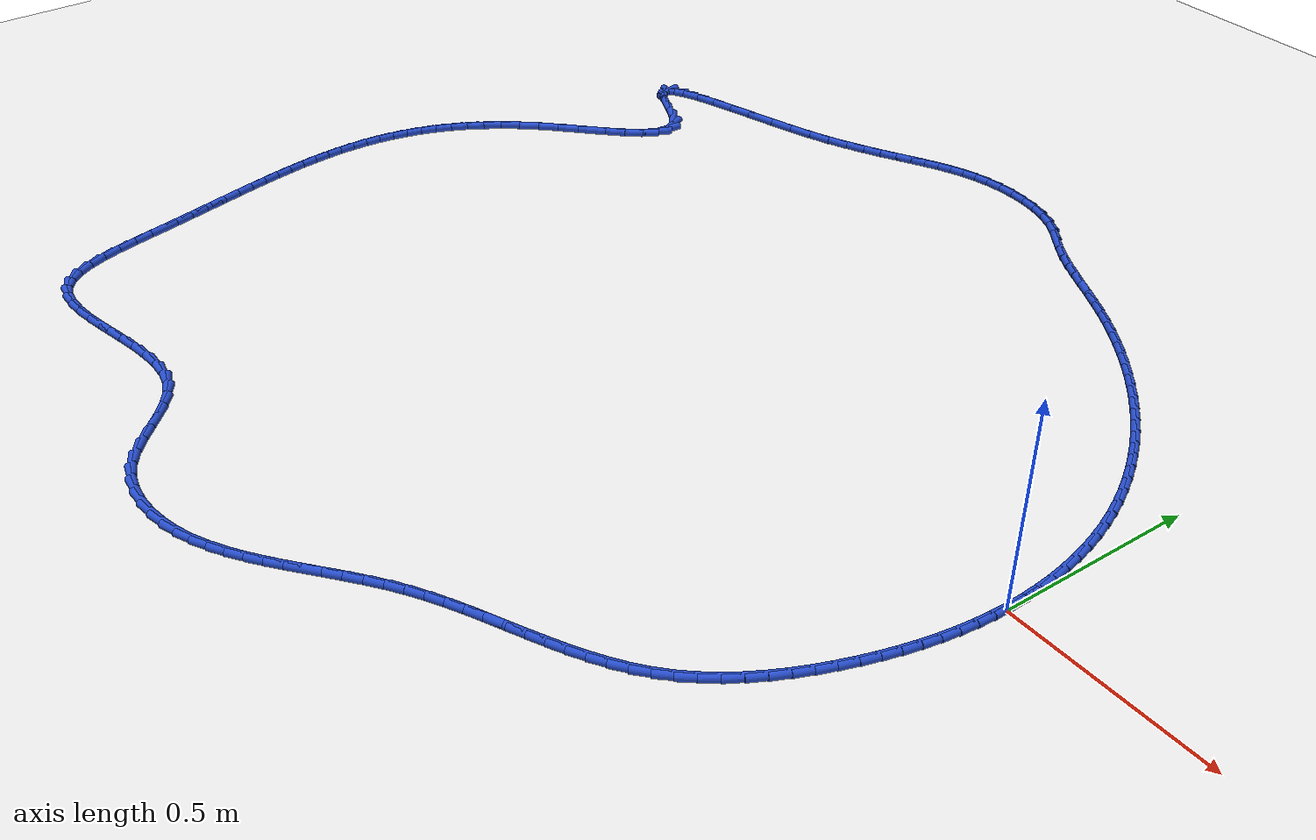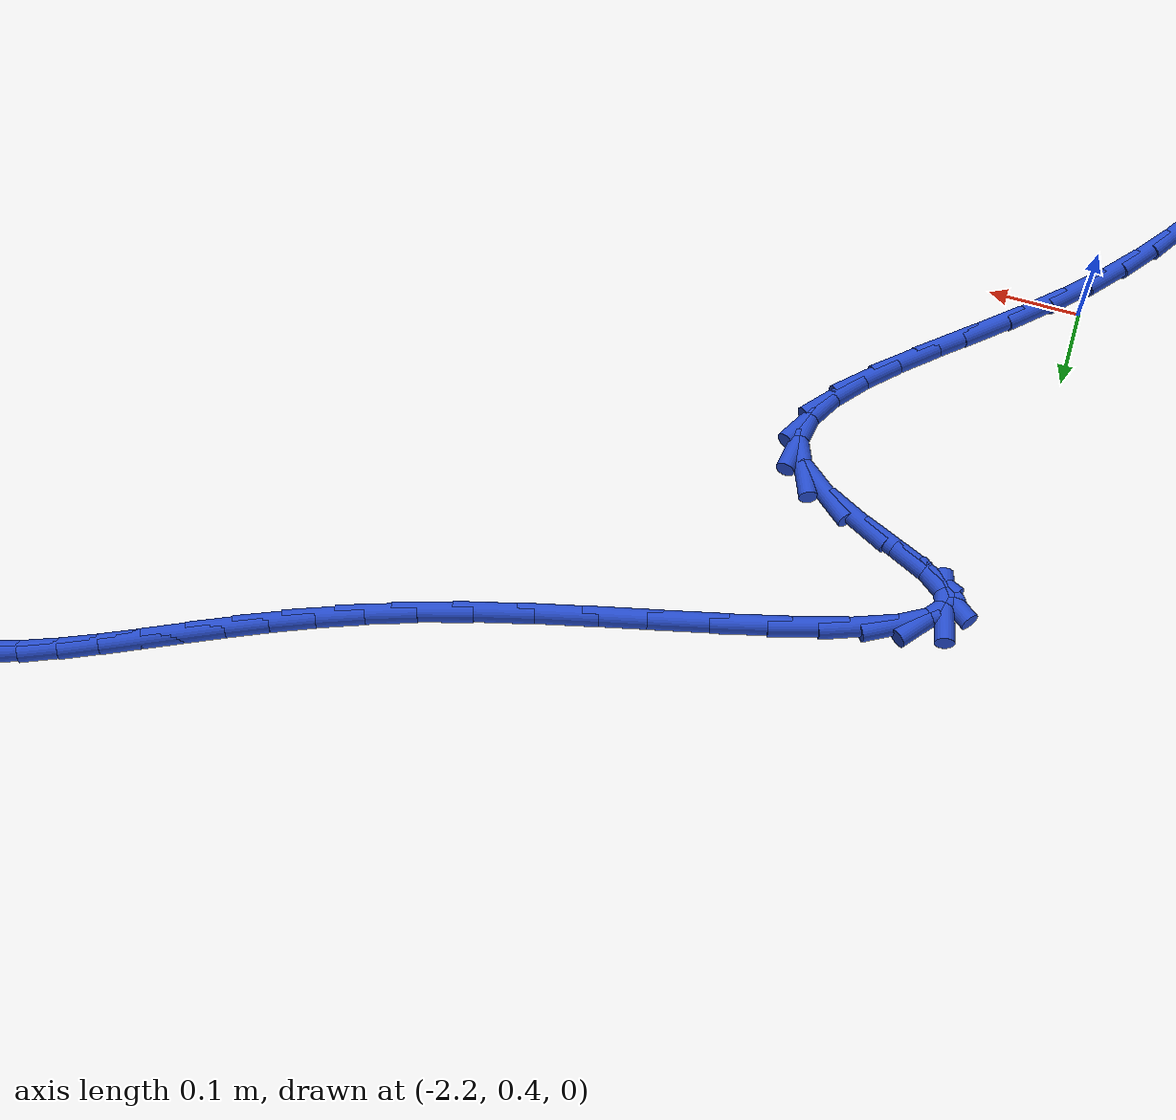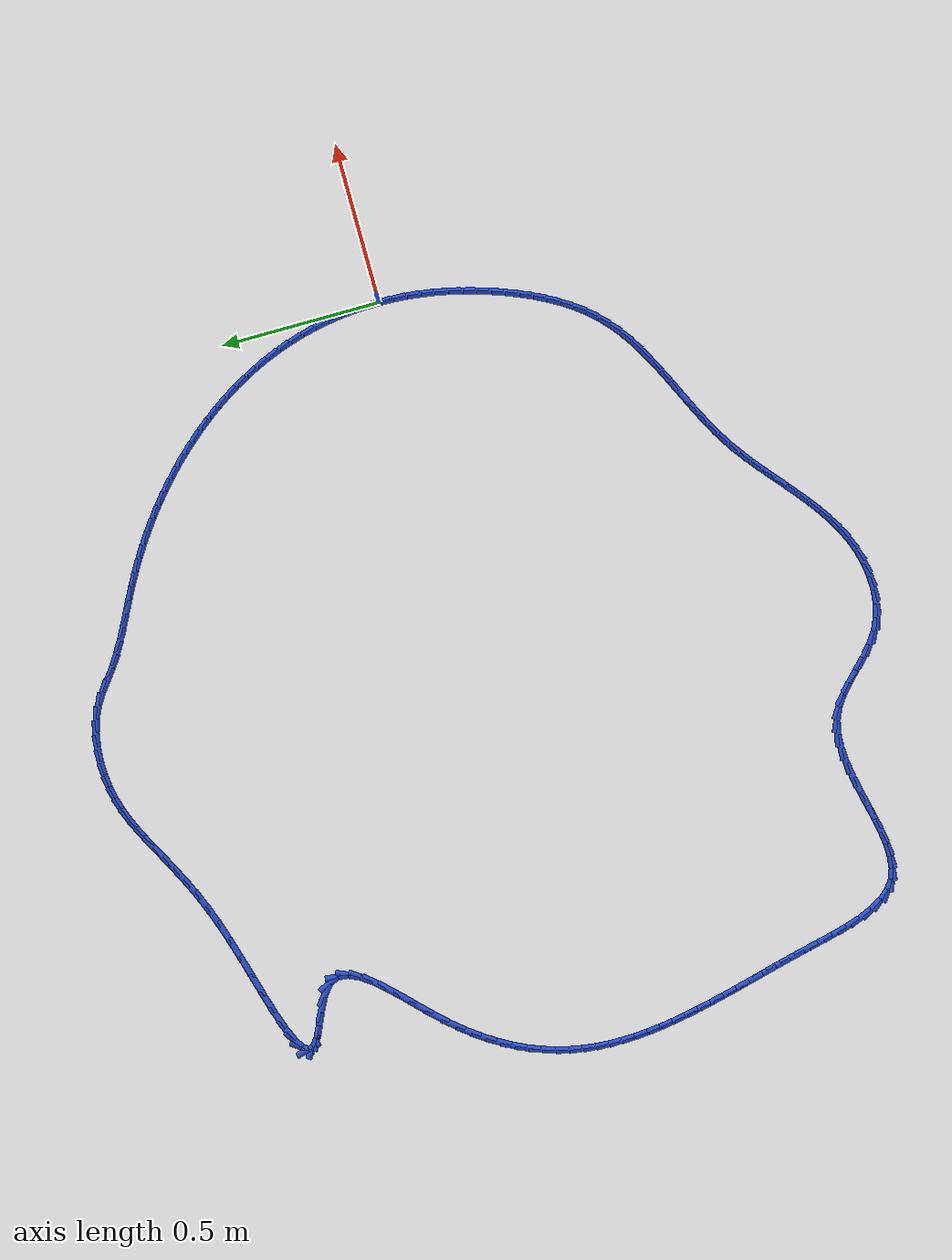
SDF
<sdf version="1.6">
 <world name="default">
  <light name="sun" type="directional">
   <pose>0 0 10 0 -0 0</pose>
   <diffuse>0.8 0.8 0.8 1</diffuse>
   <specular>0.2 0.2 0.2 1</specular>
   <attenuation>
    <range>1000</range>
    <constant>0.9</constant>
    <linear>0.01</linear>
    <quadratic>0.001</quadratic>
   </attenuation>
   <direction>-0.5 0.1 -0.9</direction>
  </light>
  <model name="ground_plane">
   <static>1</static>
   <link name="link">
    <collision name="collision">
     <geometry><plane><normal>0 0 1</normal><size>100 100</size></plane></geometry>
     <surface><friction><ode><mu>100</mu><mu2>50</mu2></ode></friction></surface>
    </collision>
    <visual name="visual">
     <cast_shadows>0</cast_shadows>
     <geometry><plane><normal>0 0 1</normal><size>100 100</size></plane></geometry>
     <material>
      <script><uri>file://media/materials/scripts/gazebo.material</uri><name>Gazebo/WhiteGlow</name></script>
     </material>
    </visual>
   </link>
  </model>
  <gravity>0 0 -9.8</gravity>
  <magnetic_field>6e-06 2.3e-05 -4.2e-05</magnetic_field>
  <atmosphere type="adiabatic"/>
  <physics name="default_physics" default="0" type="ode">
   <max_step_size>0.001</max_step_size>
   <real_time_factor>1</real_time_factor>
   <real_time_update_rate>1000</real_time_update_rate>
  </physics>
  <scene><ambient>0.4 0.4 0.4 1</ambient><background>0.7 0.7 0.7 1</background><shadows>1</shadows></scene>
  <spherical_coordinates>
   <surface_model>EARTH_WGS84</surface_model>
   <latitude_deg>0</latitude_deg>
   <longitude_deg>0</longitude_deg>
   <elevation>0</elevation>
   <heading_deg>0</heading_deg>
  </spherical_coordinates>
  <model name="line">
   <link name="link_0">
    <pose>1.0408340855860843e-17 -9.020562075079397e-17 0.01 0 1.57 -1.5546237465888721</pose>
    <collision name="collision">
     <geometry><cylinder><radius>0.01</radius><length>0.08</length></cylinder></geometry>
    </collision>
    <visual name="visual">
     <material>
      <script><name>Gazebo/Blue</name><uri>file://media/materials/scripts/gazebo.material</uri></script>
     </material>
     <geometry><cylinder><radius>0.01</radius><length>0.08</length></cylinder></geometry>
    </visual>
   </link>
   <link name="link_1">
    <pose>-0.0006884592536285922 0.042565825681515346 0.01 0 1.57 -1.5107210245905396</pose>
    <collision name="collision">
     <geometry><cylinder><radius>0.01</radius><length>0.08</length></cylinder></geometry>
    </collision>
    <visual name="visual">
     <material>
      <script><name>Gazebo/Blue</name><uri>file://media/materials/scripts/gazebo.material</uri></script>
     </material>
     <geometry><cylinder><radius>0.01</radius><length>0.08</length></cylinder></geometry>
    </visual>
   </link>
   <link name="link_2">
    <pose>-0.0032502172372238136 0.08515696242646373 0.01 0 1.57 -1.4668751654324093</pose>
    <collision name="collision">
     <geometry><cylinder><radius>0.01</radius><length>0.08</length></cylinder></geometry>
    </collision>
    <visual name="visual">
     <material>
      <script><name>Gazebo/Blue</name><uri>file://media/materials/scripts/gazebo.material</uri></script>
     </material>
     <geometry><cylinder><radius>0.01</radius><length>0.08</length></cylinder></geometry>
    </visual>
   </link>
   <link name="link_3">
    <pose>-0.007684354621984845 0.12767153316151478 0.01 0 1.57 -1.4229419530618141</pose>
    <collision name="collision">
     <geometry><cylinder><radius>0.01</radius><length>0.08</length></cylinder></geometry>
    </collision>
    <visual name="visual">
     <material>
      <script><name>Gazebo/Blue</name><uri>file://media/materials/scripts/gazebo.material</uri></script>
     </material>
     <geometry><cylinder><radius>0.01</radius><length>0.08</length></cylinder></geometry>
    </visual>
   </link>
   <link name="link_4">
    <pose>-0.013989952079110876 0.17000766081333846 0.01 0 1.57 -1.378779926097526</pose>
    <collision name="collision">
     <geometry><cylinder><radius>0.01</radius><length>0.08</length></cylinder></geometry>
    </collision>
    <visual name="visual">
     <material>
      <script><name>Gazebo/Blue</name><uri>file://media/materials/scripts/gazebo.material</uri></script>
     </material>
     <geometry><cylinder><radius>0.01</radius><length>0.08</length></cylinder></geometry>
    </visual>
   </link>
   <link name="link_5">
    <pose>-0.022166090279801084 0.21206346830860454 0.01 0 1.57 -1.3342511522537939</pose>
    <collision name="collision">
     <geometry><cylinder><radius>0.01</radius><length>0.08</length></cylinder></geometry>
    </collision>
    <visual name="visual">
     <material>
      <script><name>Gazebo/Blue</name><uri>file://media/materials/scripts/gazebo.material</uri></script>
     </material>
     <geometry><cylinder><radius>0.01</radius><length>0.08</length></cylinder></geometry>
    </visual>
   </link>
   <link name="link_6">
    <pose>-0.03221184989525467 0.25373707857398287 0.01 0 1.57 -1.289222159543858</pose>
    <collision name="collision">
     <geometry><cylinder><radius>0.01</radius><length>0.08</length></cylinder></geometry>
    </collision>
    <visual name="visual">
     <material>
      <script><name>Gazebo/Blue</name><uri>file://media/materials/scripts/gazebo.material</uri></script>
     </material>
     <geometry><cylinder><radius>0.01</radius><length>0.08</length></cylinder></geometry>
    </visual>
   </link>
   <link name="link_7">
    <pose>-0.044126311596670825 0.2949266145361432 0.01 0 1.57 -1.2435650959692932</pose>
    <collision name="collision">
     <geometry><cylinder><radius>0.01</radius><length>0.08</length></cylinder></geometry>
    </collision>
    <visual name="visual">
     <material>
      <script><name>Gazebo/Blue</name><uri>file://media/materials/scripts/gazebo.material</uri></script>
     </material>
     <geometry><cylinder><radius>0.01</radius><length>0.08</length></cylinder></geometry>
    </visual>
   </link>
   <link name="link_8">
    <pose>-0.05790855605524872 0.3355301991217555 0.01 0 1.57 -1.1973716169454367</pose>
    <collision name="collision">
     <geometry><cylinder><radius>0.01</radius><length>0.08</length></cylinder></geometry>
    </collision>
    <visual name="visual">
     <material>
      <script><name>Gazebo/Blue</name><uri>file://media/materials/scripts/gazebo.material</uri></script>
     </material>
     <geometry><cylinder><radius>0.01</radius><length>0.08</length></cylinder></geometry>
    </visual>
   </link>
   <link name="link_9">
    <pose>-0.07355068104961641 0.3754530993383196 0.01 0 1.57 -1.1519583990495712</pose>
    <collision name="collision">
     <geometry><cylinder><radius>0.01</radius><length>0.08</length></cylinder></geometry>
    </collision>
    <visual name="visual">
     <material>
      <script><name>Gazebo/Blue</name><uri>file://media/materials/scripts/gazebo.material</uri></script>
     </material>
     <geometry><cylinder><radius>0.01</radius><length>0.08</length></cylinder></geometry>
    </visual>
   </link>
   <link name="link_10">
    <pose>-0.0909991295758974 0.41464729083924035 0.01 0 1.57 -1.1078825353732706</pose>
    <collision name="collision">
     <geometry><cylinder><radius>0.01</radius><length>0.08</length></cylinder></geometry>
    </collision>
    <visual name="visual">
     <material>
      <script><name>Gazebo/Blue</name><uri>file://media/materials/scripts/gazebo.material</uri></script>
     </material>
     <geometry><cylinder><radius>0.01</radius><length>0.08</length></cylinder></geometry>
    </visual>
   </link>
   <link name="link_11">
    <pose>-0.11018199952944982 0.45308351784429574 0.01 0 1.57 -1.0651360473864284</pose>
    <collision name="collision">
     <geometry><cylinder><radius>0.01</radius><length>0.08</length></cylinder></geometry>
    </collision>
    <visual name="visual">
     <material>
      <script><name>Gazebo/Blue</name><uri>file://media/materials/scripts/gazebo.material</uri></script>
     </material>
     <geometry><cylinder><radius>0.01</radius><length>0.08</length></cylinder></geometry>
    </visual>
   </link>
   <link name="link_12">
    <pose>-0.1310273390686445 0.490732575458346 0.01 0 1.57 -1.023691318211184</pose>
    <collision name="collision">
     <geometry><cylinder><radius>0.01</radius><length>0.08</length></cylinder></geometry>
    </collision>
    <visual name="visual">
     <material>
      <script><name>Gazebo/Blue</name><uri>file://media/materials/scripts/gazebo.material</uri></script>
     </material>
     <geometry><cylinder><radius>0.01</radius><length>0.08</length></cylinder></geometry>
    </visual>
   </link>
   <link name="link_13">
    <pose>-0.15346319635185235 0.5275652587862515 0.01 0 1.57 -0.9835054612642777</pose>
    <collision name="collision">
     <geometry><cylinder><radius>0.01</radius><length>0.08</length></cylinder></geometry>
    </collision>
    <visual name="visual">
     <material>
      <script><name>Gazebo/Blue</name><uri>file://media/materials/scripts/gazebo.material</uri></script>
     </material>
     <geometry><cylinder><radius>0.01</radius><length>0.08</length></cylinder></geometry>
    </visual>
   </link>
   <link name="link_14">
    <pose>-0.17741761953744398 0.5635523629328721 0.01 0 1.57 -0.9445230080466954</pose>
    <collision name="collision">
     <geometry><cylinder><radius>0.01</radius><length>0.08</length></cylinder></geometry>
    </collision>
    <visual name="visual">
     <material>
      <script><name>Gazebo/Blue</name><uri>file://media/materials/scripts/gazebo.material</uri></script>
     </material>
     <geometry><cylinder><radius>0.01</radius><length>0.08</length></cylinder></geometry>
    </visual>
   </link>
   <link name="link_15">
    <pose>-0.20281865678379035 0.5986646830030683 0.01 0 1.57 -0.9066783392365816</pose>
    <collision name="collision">
     <geometry><cylinder><radius>0.01</radius><length>0.08</length></cylinder></geometry>
    </collision>
    <visual name="visual">
     <material>
      <script><name>Gazebo/Blue</name><uri>file://media/materials/scripts/gazebo.material</uri></script>
     </material>
     <geometry><cylinder><radius>0.01</radius><length>0.08</length></cylinder></geometry>
    </visual>
   </link>
   <link name="link_16">
    <pose>-0.22959435624926208 0.6328730141016998 0.01 0 1.57 -0.869897808555295</pose>
    <collision name="collision">
     <geometry><cylinder><radius>0.01</radius><length>0.08</length></cylinder></geometry>
    </collision>
    <visual name="visual">
     <material>
      <script><name>Gazebo/Blue</name><uri>file://media/materials/scripts/gazebo.material</uri></script>
     </material>
     <geometry><cylinder><radius>0.01</radius><length>0.08</length></cylinder></geometry>
    </visual>
   </link>
   <link name="link_17">
    <pose>-0.25767276609223 0.6661481513336269 0.01 0 1.57 -0.8341015389909325</pose>
    <collision name="collision">
     <geometry><cylinder><radius>0.01</radius><length>0.08</length></cylinder></geometry>
    </collision>
    <visual name="visual">
     <material>
      <script><name>Gazebo/Blue</name><uri>file://media/materials/scripts/gazebo.material</uri></script>
     </material>
     <geometry><cylinder><radius>0.01</radius><length>0.08</length></cylinder></geometry>
    </visual>
   </link>
   <link name="link_18">
    <pose>-0.28698193447106496 0.6984608898037096 0.01 0 1.57 -0.7992048929246198</pose>
    <collision name="collision">
     <geometry><cylinder><radius>0.01</radius><length>0.08</length></cylinder></geometry>
    </collision>
    <visual name="visual">
     <material>
      <script><name>Gazebo/Blue</name><uri>file://media/materials/scripts/gazebo.material</uri></script>
     </material>
     <geometry><cylinder><radius>0.01</radius><length>0.08</length></cylinder></geometry>
    </visual>
   </link>
   <link name="link_19">
    <pose>-0.31744990954413765 0.729782024616808 0.01 0 1.57 -0.765119632409637</pose>
    <collision name="collision">
     <geometry><cylinder><radius>0.01</radius><length>0.08</length></cylinder></geometry>
    </collision>
    <visual name="visual">
     <material>
      <script><name>Gazebo/Blue</name><uri>file://media/materials/scripts/gazebo.material</uri></script>
     </material>
     <geometry><cylinder><radius>0.01</radius><length>0.08</length></cylinder></geometry>
    </visual>
   </link>
   <link name="link_20">
    <pose>-0.3490047394698191 0.7600823508777829 0.01 0 1.57 -0.7317547946205222</pose>
    <collision name="collision">
     <geometry><cylinder><radius>0.01</radius><length>0.08</length></cylinder></geometry>
    </collision>
    <visual name="visual">
     <material>
      <script><name>Gazebo/Blue</name><uri>file://media/materials/scripts/gazebo.material</uri></script>
     </material>
     <geometry><cylinder><radius>0.01</radius><length>0.08</length></cylinder></geometry>
    </visual>
   </link>
   <link name="link_21">
    <pose>-0.38157447240647974 0.7893326636914932 0.01 0 1.57 -0.6990173117292043</pose>
    <collision name="collision">
     <geometry><cylinder><radius>0.01</radius><length>0.08</length></cylinder></geometry>
    </collision>
    <visual name="visual">
     <material>
      <script><name>Gazebo/Blue</name><uri>file://media/materials/scripts/gazebo.material</uri></script>
     </material>
     <geometry><cylinder><radius>0.01</radius><length>0.08</length></cylinder></geometry>
    </visual>
   </link>
   <link name="link_22">
    <pose>-0.41508715651249073 0.8175037581628002 0.01 0 1.57 -0.6668124054837108</pose>
    <collision name="collision">
     <geometry><cylinder><radius>0.01</radius><length>0.08</length></cylinder></geometry>
    </collision>
    <visual name="visual">
     <material>
      <script><name>Gazebo/Blue</name><uri>file://media/materials/scripts/gazebo.material</uri></script>
     </material>
     <geometry><cylinder><radius>0.01</radius><length>0.08</length></cylinder></geometry>
    </visual>
   </link>
   <link name="link_23">
    <pose>-0.4494708399462225 0.8445664293965631 0.01 0 1.57 -0.6350437856710014</pose>
    <collision name="collision">
     <geometry><cylinder><radius>0.01</radius><length>0.08</length></cylinder></geometry>
    </collision>
    <visual name="visual">
     <material>
      <script><name>Gazebo/Blue</name><uri>file://media/materials/scripts/gazebo.material</uri></script>
     </material>
     <geometry><cylinder><radius>0.01</radius><length>0.08</length></cylinder></geometry>
    </visual>
   </link>
   <link name="link_24">
    <pose>-0.4846535708660458 0.8704914724976424 0.01 0 1.57 -0.6036136793202108</pose>
    <collision name="collision">
     <geometry><cylinder><radius>0.01</radius><length>0.08</length></cylinder></geometry>
    </collision>
    <visual name="visual">
     <material>
      <script><name>Gazebo/Blue</name><uri>file://media/materials/scripts/gazebo.material</uri></script>
     </material>
     <geometry><cylinder><radius>0.01</radius><length>0.08</length></cylinder></geometry>
    </visual>
   </link>
   <link name="link_25">
    <pose>-0.5205633974303319 0.8952496825708984 0.01 0 1.57 -0.5724227146235553</pose>
    <collision name="collision">
     <geometry><cylinder><radius>0.01</radius><length>0.08</length></cylinder></geometry>
    </collision>
    <visual name="visual">
     <material>
      <script><name>Gazebo/Blue</name><uri>file://media/materials/scripts/gazebo.material</uri></script>
     </material>
     <geometry><cylinder><radius>0.01</radius><length>0.08</length></cylinder></geometry>
    </visual>
   </link>
   <link name="link_26">
    <pose>-0.5571283677974513 0.9188118547211913 0.01 0 1.57 -0.5413696806217454</pose>
    <collision name="collision">
     <geometry><cylinder><radius>0.01</radius><length>0.08</length></cylinder></geometry>
    </collision>
    <visual name="visual">
     <material>
      <script><name>Gazebo/Blue</name><uri>file://media/materials/scripts/gazebo.material</uri></script>
     </material>
     <geometry><cylinder><radius>0.01</radius><length>0.08</length></cylinder></geometry>
    </visual>
   </link>
   <link name="link_27">
    <pose>-0.5942765301257746 0.9411487840533805 0.01 0 1.57 -0.5105320126616849</pose>
    <collision name="collision">
     <geometry><cylinder><radius>0.01</radius><length>0.08</length></cylinder></geometry>
    </collision>
    <visual name="visual">
     <material>
      <script><name>Gazebo/Blue</name><uri>file://media/materials/scripts/gazebo.material</uri></script>
     </material>
     <geometry><cylinder><radius>0.01</radius><length>0.08</length></cylinder></geometry>
    </visual>
   </link>
   <link name="link_28">
    <pose>-0.631933201665996 0.9622386813665975 0.01 0 1.57 -0.48584645287184763</pose>
    <collision name="collision">
     <geometry><cylinder><radius>0.01</radius><length>0.08</length></cylinder></geometry>
    </collision>
    <visual name="visual">
     <material>
      <script><name>Gazebo/Blue</name><uri>file://media/materials/scripts/gazebo.material</uri></script>
     </material>
     <geometry><cylinder><radius>0.01</radius><length>0.08</length></cylinder></geometry>
    </visual>
   </link>
   <link name="link_29">
    <pose>-0.6699333136602075 0.9823051978356452 0.01 0 1.57 -0.47468371696506817</pose>
    <collision name="collision">
     <geometry><cylinder><radius>0.01</radius><length>0.08</length></cylinder></geometry>
    </collision>
    <visual name="visual">
     <material>
      <script><name>Gazebo/Blue</name><uri>file://media/materials/scripts/gazebo.material</uri></script>
     </material>
     <geometry><cylinder><radius>0.01</radius><length>0.08</length></cylinder></geometry>
    </visual>
   </link>
   <link name="link_30">
    <pose>-0.70800277313496 1.0018680364782344 0.01 0 1.57 -0.477651220388469</pose>
    <collision name="collision">
     <geometry><cylinder><radius>0.01</radius><length>0.08</length></cylinder></geometry>
    </collision>
    <visual name="visual">
     <material>
      <script><name>Gazebo/Blue</name><uri>file://media/materials/scripts/gazebo.material</uri></script>
     </material>
     <geometry><cylinder><radius>0.01</radius><length>0.08</length></cylinder></geometry>
    </visual>
   </link>
   <link name="link_31">
    <pose>-0.7458609874469772 1.021464549961938 0.01 0 1.57 -0.49491977417133604</pose>
    <collision name="collision">
     <geometry><cylinder><radius>0.01</radius><length>0.08</length></cylinder></geometry>
    </collision>
    <visual name="visual">
     <material>
      <script><name>Gazebo/Blue</name><uri>file://media/materials/scripts/gazebo.material</uri></script>
     </material>
     <geometry><cylinder><radius>0.01</radius><length>0.08</length></cylinder></geometry>
    </visual>
   </link>
   <link name="link_32">
    <pose>-0.7832273639529822 1.0416320909543288 0.01 0 1.57 -0.5266348512514808</pose>
    <collision name="collision">
     <geometry><cylinder><radius>0.01</radius><length>0.08</length></cylinder></geometry>
    </collision>
    <visual name="visual">
     <material>
      <script><name>Gazebo/Blue</name><uri>file://media/materials/scripts/gazebo.material</uri></script>
     </material>
     <geometry><cylinder><radius>0.01</radius><length>0.08</length></cylinder></geometry>
    </visual>
   </link>
   <link name="link_33">
    <pose>-0.8198213100096992 1.0629080121229801 0.01 0 1.57 -0.5728077115171814</pose>
    <collision name="collision">
     <geometry><cylinder><radius>0.01</radius><length>0.08</length></cylinder></geometry>
    </collision>
    <visual name="visual">
     <material>
      <script><name>Gazebo/Blue</name><uri>file://media/materials/scripts/gazebo.material</uri></script>
     </material>
     <geometry><cylinder><radius>0.01</radius><length>0.08</length></cylinder></geometry>
    </visual>
   </link>
   <link name="link_34">
    <pose>-0.855362232973851 1.085829666135465 0.01 0 1.57 -0.6316696101390062</pose>
    <collision name="collision">
     <geometry><cylinder><radius>0.01</radius><length>0.08</length></cylinder></geometry>
    </collision>
    <visual name="visual">
     <material>
      <script><name>Gazebo/Blue</name><uri>file://media/materials/scripts/gazebo.material</uri></script>
     </material>
     <geometry><cylinder><radius>0.01</radius><length>0.08</length></cylinder></geometry>
    </visual>
   </link>
   <link name="link_35">
    <pose>-0.8896026371467843 1.1108825151292092 0.01 0 1.57 -0.6529490936604984</pose>
    <collision name="collision">
     <geometry><cylinder><radius>0.01</radius><length>0.08</length></cylinder></geometry>
    </collision>
    <visual name="visual">
     <material>
      <script><name>Gazebo/Blue</name><uri>file://media/materials/scripts/gazebo.material</uri></script>
     </material>
     <geometry><cylinder><radius>0.01</radius><length>0.08</length></cylinder></geometry>
    </visual>
   </link>
   <link name="link_36">
    <pose>-0.9234371073739399 1.1367614280138056 0.01 0 1.57 -0.5758726116651455</pose>
    <collision name="collision">
     <geometry><cylinder><radius>0.01</radius><length>0.08</length></cylinder></geometry>
    </collision>
    <visual name="visual">
     <material>
      <script><name>Gazebo/Blue</name><uri>file://media/materials/scripts/gazebo.material</uri></script>
     </material>
     <geometry><cylinder><radius>0.01</radius><length>0.08</length></cylinder></geometry>
    </visual>
   </link>
   <link name="link_37">
    <pose>-0.9591648334395042 1.1599589143588405 0.01 0 1.57 -0.42508671259304603</pose>
    <collision name="collision">
     <geometry><cylinder><radius>0.01</radius><length>0.08</length></cylinder></geometry>
    </collision>
    <visual name="visual">
     <material>
      <script><name>Gazebo/Blue</name><uri>file://media/materials/scripts/gazebo.material</uri></script>
     </material>
     <geometry><cylinder><radius>0.01</radius><length>0.08</length></cylinder></geometry>
    </visual>
   </link>
   <link name="link_38">
    <pose>-0.9983924084643259 1.1777167523506915 0.01 0 1.57 -0.2852124911612364</pose>
    <collision name="collision">
     <geometry><cylinder><radius>0.01</radius><length>0.08</length></cylinder></geometry>
    </collision>
    <visual name="visual">
     <material>
      <script><name>Gazebo/Blue</name><uri>file://media/materials/scripts/gazebo.material</uri></script>
     </material>
     <geometry><cylinder><radius>0.01</radius><length>0.08</length></cylinder></geometry>
    </visual>
   </link>
   <link name="link_39">
    <pose>-1.0403196967751573 1.1900100994200227 0.01 0 1.57 -0.16745886402935106</pose>
    <collision name="collision">
     <geometry><cylinder><radius>0.01</radius><length>0.08</length></cylinder></geometry>
    </collision>
    <visual name="visual">
     <material>
      <script><name>Gazebo/Blue</name><uri>file://media/materials/scripts/gazebo.material</uri></script>
     </material>
     <geometry><cylinder><radius>0.01</radius><length>0.08</length></cylinder></geometry>
    </visual>
   </link>
   <link name="link_40">
    <pose>-1.0836832113096664 1.197340352211836 0.01 0 1.57 -0.06579378256976819</pose>
    <collision name="collision">
     <geometry><cylinder><radius>0.01</radius><length>0.08</length></cylinder></geometry>
    </collision>
    <visual name="visual">
     <material>
      <script><name>Gazebo/Blue</name><uri>file://media/materials/scripts/gazebo.material</uri></script>
     </material>
     <geometry><cylinder><radius>0.01</radius><length>0.08</length></cylinder></geometry>
    </visual>
   </link>
   <link name="link_41">
    <pose>-1.1272194650055205 1.2002089073711333 0.01 0 1.57 0.025715447271346066</pose>
    <collision name="collision">
     <geometry><cylinder><radius>0.01</radius><length>0.08</length></cylinder></geometry>
    </collision>
    <visual name="visual">
     <material>
      <script><name>Gazebo/Blue</name><uri>file://media/materials/scripts/gazebo.material</uri></script>
     </material>
     <geometry><cylinder><radius>0.01</radius><length>0.08</length></cylinder></geometry>
    </visual>
   </link>
   <link name="link_42">
    <pose>-1.1696649708003894 1.1991171615429173 0.01 0 1.57 0.11299402862763544</pose>
    <collision name="collision">
     <geometry><cylinder><radius>0.01</radius><length>0.08</length></cylinder></geometry>
    </collision>
    <visual name="visual">
     <material>
      <script><name>Gazebo/Blue</name><uri>file://media/materials/scripts/gazebo.material</uri></script>
     </material>
     <geometry><cylinder><radius>0.01</radius><length>0.08</length></cylinder></geometry>
    </visual>
   </link>
   <link name="link_43">
    <pose>-1.209822662102155 1.1945601716765206 0.01 0 1.57 0.19961256746631506</pose>
    <collision name="collision">
     <geometry><cylinder><radius>0.01</radius><length>0.08</length></cylinder></geometry>
    </collision>
    <visual name="visual">
     <material>
      <script><name>Gazebo/Blue</name><uri>file://media/materials/scripts/gazebo.material</uri></script>
     </material>
     <geometry><cylinder><radius>0.01</radius><length>0.08</length></cylinder></geometry>
    </visual>
   </link>
   <link name="link_44">
    <pose>-1.2475063503512294 1.1869365085165675 0.01 0 1.57 0.28178966671346406</pose>
    <collision name="collision">
     <geometry><cylinder><radius>0.01</radius><length>0.08</length></cylinder></geometry>
    </collision>
    <visual name="visual">
     <material>
      <script><name>Gazebo/Blue</name><uri>file://media/materials/scripts/gazebo.material</uri></script>
     </material>
     <geometry><cylinder><radius>0.01</radius><length>0.08</length></cylinder></geometry>
    </visual>
   </link>
   <link name="link_45">
    <pose>-1.283316826397569 1.1765696272606374 0.01 0 1.57 0.3544273733527806</pose>
    <collision name="collision">
     <geometry><cylinder><radius>0.01</radius><length>0.08</length></cylinder></geometry>
    </collision>
    <visual name="visual">
     <material>
      <script><name>Gazebo/Blue</name><uri>file://media/materials/scripts/gazebo.material</uri></script>
     </material>
     <geometry><cylinder><radius>0.01</radius><length>0.08</length></cylinder></geometry>
    </visual>
   </link>
   <link name="link_46">
    <pose>-1.3178756400389573 1.163781001707937 0.01 0 1.57 0.41352533868249486</pose>
    <collision name="collision">
     <geometry><cylinder><radius>0.01</radius><length>0.08</length></cylinder></geometry>
    </collision>
    <visual name="visual">
     <material>
      <script><name>Gazebo/Blue</name><uri>file://media/materials/scripts/gazebo.material</uri></script>
     </material>
     <geometry><cylinder><radius>0.01</radius><length>0.08</length></cylinder></geometry>
    </visual>
   </link>
   <link name="link_47">
    <pose>-1.3518043410731768 1.1488921056576715 0.01 0 1.57 0.45672822138737235</pose>
    <collision name="collision">
     <geometry><cylinder><radius>0.01</radius><length>0.08</length></cylinder></geometry>
    </collision>
    <visual name="visual">
     <material>
      <script><name>Gazebo/Blue</name><uri>file://media/materials/scripts/gazebo.material</uri></script>
     </material>
     <geometry><cylinder><radius>0.01</radius><length>0.08</length></cylinder></geometry>
    </visual>
   </link>
   <link name="link_48">
    <pose>-1.3857244792980108 1.1322244129090475 0.01 0 1.57 0.4833363267304123</pose>
    <collision name="collision">
     <geometry><cylinder><radius>0.01</radius><length>0.08</length></cylinder></geometry>
    </collision>
    <visual name="visual">
     <material>
      <script><name>Gazebo/Blue</name><uri>file://media/materials/scripts/gazebo.material</uri></script>
     </material>
     <geometry><cylinder><radius>0.01</radius><length>0.08</length></cylinder></geometry>
    </visual>
   </link>
   <link name="link_49">
    <pose>-1.420257604511242 1.1140993972612707 0.01 0 1.57 0.49397072463543995</pose>
    <collision name="collision">
     <geometry><cylinder><radius>0.01</radius><length>0.08</length></cylinder></geometry>
    </collision>
    <visual name="visual">
     <material>
      <script><name>Gazebo/Blue</name><uri>file://media/materials/scripts/gazebo.material</uri></script>
     </material>
     <geometry><cylinder><radius>0.01</radius><length>0.08</length></cylinder></geometry>
    </visual>
   </link>
   <link name="link_50">
    <pose>-1.4560252665106543 1.0948385325135481 0.01 0 1.57 0.4901485263367006</pose>
    <collision name="collision">
     <geometry><cylinder><radius>0.01</radius><length>0.08</length></cylinder></geometry>
    </collision>
    <visual name="visual">
     <material>
      <script><name>Gazebo/Blue</name><uri>file://media/materials/scripts/gazebo.material</uri></script>
     </material>
     <geometry><cylinder><radius>0.01</radius><length>0.08</length></cylinder></geometry>
    </visual>
   </link>
   <link name="link_51">
    <pose>-1.4936490150940291 1.0747632924650845 0.01 0 1.57 0.47391705817769164</pose>
    <collision name="collision">
     <geometry><cylinder><radius>0.01</radius><length>0.08</length></cylinder></geometry>
    </collision>
    <visual name="visual">
     <material>
      <script><name>Gazebo/Blue</name><uri>file://media/materials/scripts/gazebo.material</uri></script>
     </material>
     <geometry><cylinder><radius>0.01</radius><length>0.08</length></cylinder></geometry>
    </visual>
   </link>
   <link name="link_52">
    <pose>-1.5337504000591498 1.0541951509150858 0.01 0 1.57 0.44758196495877295</pose>
    <collision name="collision">
     <geometry><cylinder><radius>0.01</radius><length>0.08</length></cylinder></geometry>
    </collision>
    <visual name="visual">
     <material>
      <script><name>Gazebo/Blue</name><uri>file://media/materials/scripts/gazebo.material</uri></script>
     </material>
     <geometry><cylinder><radius>0.01</radius><length>0.08</length></cylinder></geometry>
    </visual>
   </link>
   <link name="link_53">
    <pose>-1.5769509712037995 1.0334555816627593 0.01 0 1.57 0.4135091742636895</pose>
    <collision name="collision">
     <geometry><cylinder><radius>0.01</radius><length>0.08</length></cylinder></geometry>
    </collision>
    <visual name="visual">
     <material>
      <script><name>Gazebo/Blue</name><uri>file://media/materials/scripts/gazebo.material</uri></script>
     </material>
     <geometry><cylinder><radius>0.01</radius><length>0.08</length></cylinder></geometry>
    </visual>
   </link>
   <link name="link_54">
    <pose>-1.6238722783257606 1.01286605850731 0.01 0 1.57 0.37397420376765933</pose>
    <collision name="collision">
     <geometry><cylinder><radius>0.01</radius><length>0.08</length></cylinder></geometry>
    </collision>
    <visual name="visual">
     <material>
      <script><name>Gazebo/Blue</name><uri>file://media/materials/scripts/gazebo.material</uri></script>
     </material>
     <geometry><cylinder><radius>0.01</radius><length>0.08</length></cylinder></geometry>
    </visual>
   </link>
   <link name="link_55">
    <pose>-1.6751358712228175 0.9927480552479443 0.01 0 1.57 0.3319335956265296</pose>
    <collision name="collision">
     <geometry><cylinder><radius>0.01</radius><length>0.08</length></cylinder></geometry>
    </collision>
    <visual name="visual">
     <material>
      <script><name>Gazebo/Blue</name><uri>file://media/materials/scripts/gazebo.material</uri></script>
     </material>
     <geometry><cylinder><radius>0.01</radius><length>0.08</length></cylinder></geometry>
    </visual>
   </link>
   <link name="link_56">
    <pose>-1.7312525152095901 0.9734053914166045 0.01 0 1.57 0.29953487394537726</pose>
    <collision name="collision">
     <geometry><cylinder><radius>0.01</radius><length>0.08</length></cylinder></geometry>
    </collision>
    <visual name="visual">
     <material>
      <script><name>Gazebo/Blue</name><uri>file://media/materials/scripts/gazebo.material</uri></script>
     </material>
     <geometry><cylinder><radius>0.01</radius><length>0.08</length></cylinder></geometry>
    </visual>
   </link>
   <link name="link_57">
    <pose>-1.7911880640419027 0.9548956942917733 0.01 0 1.57 0.28135613155703276</pose>
    <collision name="collision">
     <geometry><cylinder><radius>0.01</radius><length>0.08</length></cylinder></geometry>
    </collision>
    <visual name="visual">
     <material>
      <script><name>Gazebo/Blue</name><uri>file://media/materials/scripts/gazebo.material</uri></script>
     </material>
     <geometry><cylinder><radius>0.01</radius><length>0.08</length></cylinder></geometry>
    </visual>
   </link>
   <link name="link_58">
    <pose>-1.8527742471496307 0.9370958606616221 0.01 0 1.57 0.27491223835747963</pose>
    <collision name="collision">
     <geometry><cylinder><radius>0.01</radius><length>0.08</length></cylinder></geometry>
    </collision>
    <visual name="visual">
     <material>
      <script><name>Gazebo/Blue</name><uri>file://media/materials/scripts/gazebo.material</uri></script>
     </material>
     <geometry><cylinder><radius>0.01</radius><length>0.08</length></cylinder></geometry>
    </visual>
   </link>
   <link name="link_59">
    <pose>-1.9138166355756276 0.9198786187959306 0.01 0 1.57 0.2799414968257923</pose>
    <collision name="collision">
     <geometry><cylinder><radius>0.01</radius><length>0.08</length></cylinder></geometry>
    </collision>
    <visual name="visual">
     <material>
      <script><name>Gazebo/Blue</name><uri>file://media/materials/scripts/gazebo.material</uri></script>
     </material>
     <geometry><cylinder><radius>0.01</radius><length>0.08</length></cylinder></geometry>
    </visual>
   </link>
   <link name="link_60">
    <pose>-1.9721208003627486 0.9031166969644774 0.01 0 1.57 0.298702083468043</pose>
    <collision name="collision">
     <geometry><cylinder><radius>0.01</radius><length>0.08</length></cylinder></geometry>
    </collision>
    <visual name="visual">
     <material>
      <script><name>Gazebo/Blue</name><uri>file://media/materials/scripts/gazebo.material</uri></script>
     </material>
     <geometry><cylinder><radius>0.01</radius><length>0.08</length></cylinder></geometry>
    </visual>
   </link>
   <link name="link_61">
    <pose>-2.0254923125538458 0.8866828234370421 0.01 0 1.57 0.3375904725033097</pose>
    <collision name="collision">
     <geometry><cylinder><radius>0.01</radius><length>0.08</length></cylinder></geometry>
    </collision>
    <visual name="visual">
     <material>
      <script><name>Gazebo/Blue</name><uri>file://media/materials/scripts/gazebo.material</uri></script>
     </material>
     <geometry><cylinder><radius>0.01</radius><length>0.08</length></cylinder></geometry>
    </visual>
   </link>
   <link name="link_62">
    <pose>-2.071736743191776 0.8704497264834042 0.01 0 1.57 0.4125426123595328</pose>
    <collision name="collision">
     <geometry><cylinder><radius>0.01</radius><length>0.08</length></cylinder></geometry>
    </collision>
    <visual name="visual">
     <material>
      <script><name>Gazebo/Blue</name><uri>file://media/materials/scripts/gazebo.material</uri></script>
     </material>
     <geometry><cylinder><radius>0.01</radius><length>0.08</length></cylinder></geometry>
    </visual>
   </link>
   <link name="link_63">
    <pose>-2.108659663319392 0.8542901343733422 0.01 0 1.57 0.5679967028160154</pose>
    <collision name="collision">
     <geometry><cylinder><radius>0.01</radius><length>0.08</length></cylinder></geometry>
    </collision>
    <visual name="visual">
     <material>
      <script><name>Gazebo/Blue</name><uri>file://media/materials/scripts/gazebo.material</uri></script>
     </material>
     <geometry><cylinder><radius>0.01</radius><length>0.08</length></cylinder></geometry>
    </visual>
   </link>
   <link name="link_64">
    <pose>-2.1340666439795486 0.838076775376636 0.01 0 1.57 0.9510992552978907</pose>
    <collision name="collision">
     <geometry><cylinder><radius>0.01</radius><length>0.08</length></cylinder></geometry>
    </collision>
    <visual name="visual">
     <material>
      <script><name>Gazebo/Blue</name><uri>file://media/materials/scripts/gazebo.material</uri></script>
     </material>
     <geometry><cylinder><radius>0.01</radius><length>0.08</length></cylinder></geometry>
    </visual>
   </link>
   <link name="link_65">
    <pose>-2.1457632562150994 0.8216823777630649 0.01 0 1.57 -1.323986710715559</pose>
    <collision name="collision">
     <geometry><cylinder><radius>0.01</radius><length>0.08</length></cylinder></geometry>
    </collision>
    <visual name="visual">
     <material>
      <script><name>Gazebo/Blue</name><uri>file://media/materials/scripts/gazebo.material</uri></script>
     </material>
     <geometry><cylinder><radius>0.01</radius><length>0.08</length></cylinder></geometry>
    </visual>
   </link>
   <link name="link_66">
    <pose>-2.141555071068899 0.8049796698024075 0.01 0 1.57 -0.6590671369497649</pose>
    <collision name="collision">
     <geometry><cylinder><radius>0.01</radius><length>0.08</length></cylinder></geometry>
    </collision>
    <visual name="visual">
     <material>
      <script><name>Gazebo/Blue</name><uri>file://media/materials/scripts/gazebo.material</uri></script>
     </material>
     <geometry><cylinder><radius>0.01</radius><length>0.08</length></cylinder></geometry>
    </visual>
   </link>
   <link name="link_67">
    <pose>-2.1194180693554636 0.7878320996513816 0.01 0 1.57 -0.4516246391196411</pose>
    <collision name="collision">
     <geometry><cylinder><radius>0.01</radius><length>0.08</length></cylinder></geometry>
    </collision>
    <visual name="visual">
     <material>
      <script><name>Gazebo/Blue</name><uri>file://media/materials/scripts/gazebo.material</uri></script>
     </material>
     <geometry><cylinder><radius>0.01</radius><length>0.08</length></cylinder></geometry>
    </visual>
   </link>
   <link name="link_68">
    <pose>-2.082308840861149 0.7698318832836751 0.01 0 1.57 -0.4229714235238776</pose>
    <collision name="collision">
     <geometry><cylinder><radius>0.01</radius><length>0.08</length></cylinder></geometry>
    </collision>
    <visual name="visual">
     <material>
      <script><name>Gazebo/Blue</name><uri>file://media/materials/scripts/gazebo.material</uri></script>
     </material>
     <geometry><cylinder><radius>0.01</radius><length>0.08</length></cylinder></geometry>
    </visual>
   </link>
   <link name="link_69">
    <pose>-2.0388369483066606 0.7502633891390199 0.01 0 1.57 -0.4908196747301984</pose>
    <collision name="collision">
     <geometry><cylinder><radius>0.01</radius><length>0.08</length></cylinder></geometry>
    </collision>
    <visual name="visual">
     <material>
      <script><name>Gazebo/Blue</name><uri>file://media/materials/scripts/gazebo.material</uri></script>
     </material>
     <geometry><cylinder><radius>0.01</radius><length>0.08</length></cylinder></geometry>
    </visual>
   </link>
   <link name="link_70">
    <pose>-1.9979175132839162 0.7283943456438182 0.01 0 1.57 -0.701595290917189</pose>
    <collision name="collision">
     <geometry><cylinder><radius>0.01</radius><length>0.08</length></cylinder></geometry>
    </collision>
    <visual name="visual">
     <material>
      <script><name>Gazebo/Blue</name><uri>file://media/materials/scripts/gazebo.material</uri></script>
     </material>
     <geometry><cylinder><radius>0.01</radius><length>0.08</length></cylinder></geometry>
    </visual>
   </link>
   <link name="link_71">
    <pose>-1.9684503607570212 0.7034940382974834 0.01 0 1.57 -1.1588446502538432</pose>
    <collision name="collision">
     <geometry><cylinder><radius>0.01</radius><length>0.08</length></cylinder></geometry>
    </collision>
    <visual name="visual">
     <material>
      <script><name>Gazebo/Blue</name><uri>file://media/materials/scripts/gazebo.material</uri></script>
     </material>
     <geometry><cylinder><radius>0.01</radius><length>0.08</length></cylinder></geometry>
    </visual>
   </link>
   <link name="link_72">
    <pose>-1.95607144525303 0.67516398821596 0.01 0 1.57 1.4739263779926324</pose>
    <collision name="collision">
     <geometry><cylinder><radius>0.01</radius><length>0.08</length></cylinder></geometry>
    </collision>
    <visual name="visual">
     <material>
      <script><name>Gazebo/Blue</name><uri>file://media/materials/scripts/gazebo.material</uri></script>
     </material>
     <geometry><cylinder><radius>0.01</radius><length>0.08</length></cylinder></geometry>
    </visual>
   </link>
   <link name="link_73">
    <pose>-1.9591242625063365 0.6437480298483136 0.01 0 1.57 1.135465738945898</pose>
    <collision name="collision">
     <geometry><cylinder><radius>0.01</radius><length>0.08</length></cylinder></geometry>
    </collision>
    <visual name="visual">
     <material>
      <script><name>Gazebo/Blue</name><uri>file://media/materials/scripts/gazebo.material</uri></script>
     </material>
     <geometry><cylinder><radius>0.01</radius><length>0.08</length></cylinder></geometry>
    </visual>
   </link>
   <link name="link_74">
    <pose>-1.974963987404465 0.6096906007135611 0.01 0 1.57 0.9489821944028595</pose>
    <collision name="collision">
     <geometry><cylinder><radius>0.01</radius><length>0.08</length></cylinder></geometry>
    </collision>
    <visual name="visual">
     <material>
      <script><name>Gazebo/Blue</name><uri>file://media/materials/scripts/gazebo.material</uri></script>
     </material>
     <geometry><cylinder><radius>0.01</radius><length>0.08</length></cylinder></geometry>
    </visual>
   </link>
   <link name="link_75">
    <pose>-2.000945794834938 0.5734361383307197 0.01 0 1.57 0.848654528044324</pose>
    <collision name="collision">
     <geometry><cylinder><radius>0.01</radius><length>0.08</length></cylinder></geometry>
    </collision>
    <visual name="visual">
     <material>
      <script><name>Gazebo/Blue</name><uri>file://media/materials/scripts/gazebo.material</uri></script>
     </material>
     <geometry><cylinder><radius>0.01</radius><length>0.08</length></cylinder></geometry>
    </visual>
   </link>
   <link name="link_76">
    <pose>-2.034424859685278 0.5354290802188064 0.01 0 1.57 0.7980666524254405</pose>
    <collision name="collision">
     <geometry><cylinder><radius>0.01</radius><length>0.08</length></cylinder></geometry>
    </collision>
    <visual name="visual">
     <material>
      <script><name>Gazebo/Blue</name><uri>file://media/materials/scripts/gazebo.material</uri></script>
     </material>
     <geometry><cylinder><radius>0.01</radius><length>0.08</length></cylinder></geometry>
    </visual>
   </link>
   <link name="link_77">
    <pose>-2.072756356843009 0.4961138638968376 0.01 0 1.57 0.7809361504040183</pose>
    <collision name="collision">
     <geometry><cylinder><radius>0.01</radius><length>0.08</length></cylinder></geometry>
    </collision>
    <visual name="visual">
     <material>
      <script><name>Gazebo/Blue</name><uri>file://media/materials/scripts/gazebo.material</uri></script>
     </material>
     <geometry><cylinder><radius>0.01</radius><length>0.08</length></cylinder></geometry>
    </visual>
   </link>
   <link name="link_78">
    <pose>-2.113295461195654 0.4559349268838312 0.01 0 1.57 0.7915484339812228</pose>
    <collision name="collision">
     <geometry><cylinder><radius>0.01</radius><length>0.08</length></cylinder></geometry>
    </collision>
    <visual name="visual">
     <material>
      <script><name>Gazebo/Blue</name><uri>file://media/materials/scripts/gazebo.material</uri></script>
     </material>
     <geometry><cylinder><radius>0.01</radius><length>0.08</length></cylinder></geometry>
    </visual>
   </link>
   <link name="link_79">
    <pose>-2.1533973476307344 0.4153367066988035 0.01 0 1.57 0.8298150854866194</pose>
    <collision name="collision">
     <geometry><cylinder><radius>0.01</radius><length>0.08</length></cylinder></geometry>
    </collision>
    <visual name="visual">
     <material>
      <script><name>Gazebo/Blue</name><uri>file://media/materials/scripts/gazebo.material</uri></script>
     </material>
     <geometry><cylinder><radius>0.01</radius><length>0.08</length></cylinder></geometry>
    </visual>
   </link>
   <link name="link_80">
    <pose>-2.1905358220669897 0.37474335133330083 0.01 0 1.57 0.8831038718467727</pose>
    <collision name="collision">
     <geometry><cylinder><radius>0.01</radius><length>0.08</length></cylinder></geometry>
    </collision>
    <visual name="visual">
     <material>
      <script><name>Gazebo/Blue</name><uri>file://media/materials/scripts/gazebo.material</uri></script>
     </material>
     <geometry><cylinder><radius>0.01</radius><length>0.08</length></cylinder></geometry>
    </visual>
   </link>
   <link name="link_81">
    <pose>-2.223749191869602 0.3343114312761673 0.01 0 1.57 0.9400494006491185</pose>
    <collision name="collision">
     <geometry><cylinder><radius>0.01</radius><length>0.08</length></cylinder></geometry>
    </collision>
    <visual name="visual">
     <material>
      <script><name>Gazebo/Blue</name><uri>file://media/materials/scripts/gazebo.material</uri></script>
     </material>
     <geometry><cylinder><radius>0.01</radius><length>0.08</length></cylinder></geometry>
    </visual>
   </link>
   <link name="link_82">
    <pose>-2.253180763546311 0.29400852843350916 0.01 0 1.57 1.0000424222144926</pose>
    <collision name="collision">
     <geometry><cylinder><radius>0.01</radius><length>0.08</length></cylinder></geometry>
    </collision>
    <visual name="visual">
     <material>
      <script><name>Gazebo/Blue</name><uri>file://media/materials/scripts/gazebo.material</uri></script>
     </material>
     <geometry><cylinder><radius>0.01</radius><length>0.08</length></cylinder></geometry>
    </visual>
   </link>
   <link name="link_83">
    <pose>-2.278997076654959 0.25379825115069116 0.01 0 1.57 1.0625606667311316</pose>
    <collision name="collision">
     <geometry><cylinder><radius>0.01</radius><length>0.08</length></cylinder></geometry>
    </collision>
    <visual name="visual">
     <material>
      <script><name>Gazebo/Blue</name><uri>file://media/materials/scripts/gazebo.material</uri></script>
     </material>
     <geometry><cylinder><radius>0.01</radius><length>0.08</length></cylinder></geometry>
    </visual>
   </link>
   <link name="link_84">
    <pose>-2.301364670753388 0.21364420777307966 0.01 0 1.57 1.1269075592928877</pose>
    <collision name="collision">
     <geometry><cylinder><radius>0.01</radius><length>0.08</length></cylinder></geometry>
    </collision>
    <visual name="visual">
     <material>
      <script><name>Gazebo/Blue</name><uri>file://media/materials/scripts/gazebo.material</uri></script>
     </material>
     <geometry><cylinder><radius>0.01</radius><length>0.08</length></cylinder></geometry>
    </visual>
   </link>
   <link name="link_85">
    <pose>-2.32045008539944 0.17351000664603916 0.01 0 1.57 1.1922351141094962</pose>
    <collision name="collision">
     <geometry><cylinder><radius>0.01</radius><length>0.08</length></cylinder></geometry>
    </collision>
    <visual name="visual">
     <material>
      <script><name>Gazebo/Blue</name><uri>file://media/materials/scripts/gazebo.material</uri></script>
     </material>
     <geometry><cylinder><radius>0.01</radius><length>0.08</length></cylinder></geometry>
    </visual>
   </link>
   <link name="link_86">
    <pose>-2.3364198601509583 0.13335925611493615 0.01 0 1.57 1.2575889560121243</pose>
    <collision name="collision">
     <geometry><cylinder><radius>0.01</radius><length>0.08</length></cylinder></geometry>
    </collision>
    <visual name="visual">
     <material>
      <script><name>Gazebo/Blue</name><uri>file://media/materials/scripts/gazebo.material</uri></script>
     </material>
     <geometry><cylinder><radius>0.01</radius><length>0.08</length></cylinder></geometry>
    </visual>
   </link>
   <link name="link_87">
    <pose>-2.3494405345657845 0.09315556452513543 0.01 0 1.57 1.321970594206224</pose>
    <collision name="collision">
     <geometry><cylinder><radius>0.01</radius><length>0.08</length></cylinder></geometry>
    </collision>
    <visual name="visual">
     <material>
      <script><name>Gazebo/Blue</name><uri>file://media/materials/scripts/gazebo.material</uri></script>
     </material>
     <geometry><cylinder><radius>0.01</radius><length>0.08</length></cylinder></geometry>
    </visual>
   </link>
   <link name="link_88">
    <pose>-2.359678648201762 0.05286254022200202 0.01 0 1.57 1.384407057336078</pose>
    <collision name="collision">
     <geometry><cylinder><radius>0.01</radius><length>0.08</length></cylinder></geometry>
    </collision>
    <visual name="visual">
     <material>
      <script><name>Gazebo/Blue</name><uri>file://media/materials/scripts/gazebo.material</uri></script>
     </material>
     <geometry><cylinder><radius>0.01</radius><length>0.08</length></cylinder></geometry>
    </visual>
   </link>
   <link name="link_89">
    <pose>-2.367300740616732 0.01244379155090224 0.01 0 1.57 1.444015703432741</pose>
    <collision name="collision">
     <geometry><cylinder><radius>0.01</radius><length>0.08</length></cylinder></geometry>
    </collision>
    <visual name="visual">
     <material>
      <script><name>Gazebo/Blue</name><uri>file://media/materials/scripts/gazebo.material</uri></script>
     </material>
     <geometry><cylinder><radius>0.01</radius><length>0.08</length></cylinder></geometry>
    </visual>
   </link>
   <link name="link_90">
    <pose>-2.3724733513685385 -0.02813707314279896 0.01 0 1.57 1.5000535374849786</pose>
    <collision name="collision">
     <geometry><cylinder><radius>0.01</radius><length>0.08</length></cylinder></geometry>
    </collision>
    <visual name="visual">
     <material>
      <script><name>Gazebo/Blue</name><uri>file://media/materials/scripts/gazebo.material</uri></script>
     </material>
     <geometry><cylinder><radius>0.01</radius><length>0.08</length></cylinder></geometry>
    </visual>
   </link>
   <link name="link_91">
    <pose>-2.3753630200150226 -0.06891644551373607 0.01 0 1.57 1.5519449741971663</pose>
    <collision name="collision">
     <geometry><cylinder><radius>0.01</radius><length>0.08</length></cylinder></geometry>
    </collision>
    <visual name="visual">
     <material>
      <script><name>Gazebo/Blue</name><uri>file://media/materials/scripts/gazebo.material</uri></script>
     </material>
     <geometry><cylinder><radius>0.01</radius><length>0.08</length></cylinder></geometry>
    </visual>
   </link>
   <link name="link_92">
    <pose>-2.376136286114027 -0.10993071721654467 0.01 0 1.57 -1.5423050473235242</pose>
    <collision name="collision">
     <geometry><cylinder><radius>0.01</radius><length>0.08</length></cylinder></geometry>
    </collision>
    <visual name="visual">
     <material>
      <script><name>Gazebo/Blue</name><uri>file://media/materials/scripts/gazebo.material</uri></script>
     </material>
     <geometry><cylinder><radius>0.01</radius><length>0.08</length></cylinder></geometry>
    </visual>
   </link>
   <link name="link_93">
    <pose>-2.374959689223395 -0.1512162799058575 0.01 0 1.57 -1.4997526070127567</pose>
    <collision name="collision">
     <geometry><cylinder><radius>0.01</radius><length>0.08</length></cylinder></geometry>
    </collision>
    <visual name="visual">
     <material>
      <script><name>Gazebo/Blue</name><uri>file://media/materials/scripts/gazebo.material</uri></script>
     </material>
     <geometry><cylinder><radius>0.01</radius><length>0.08</length></cylinder></geometry>
    </visual>
   </link>
   <link name="link_94">
    <pose>-2.371999768900967 -0.19280952523631006 0.01 0 1.57 -1.462094488622128</pose>
    <collision name="collision">
     <geometry><cylinder><radius>0.01</radius><length>0.08</length></cylinder></geometry>
    </collision>
    <visual name="visual">
     <material>
      <script><name>Gazebo/Blue</name><uri>file://media/materials/scripts/gazebo.material</uri></script>
     </material>
     <geometry><cylinder><radius>0.01</radius><length>0.08</length></cylinder></geometry>
    </visual>
   </link>
   <link name="link_95">
    <pose>-2.3674230647045875 -0.23474684486253686 0.01 0 1.57 -1.429326552133957</pose>
    <collision name="collision">
     <geometry><cylinder><radius>0.01</radius><length>0.08</length></cylinder></geometry>
    </collision>
    <visual name="visual">
     <material>
      <script><name>Gazebo/Blue</name><uri>file://media/materials/scripts/gazebo.material</uri></script>
     </material>
     <geometry><cylinder><radius>0.01</radius><length>0.08</length></cylinder></geometry>
    </visual>
   </link>
   <link name="link_96">
    <pose>-2.3613961161920978 -0.2770646304391726 0.01 0 1.57 -1.4013655474889186</pose>
    <collision name="collision">
     <geometry><cylinder><radius>0.01</radius><length>0.08</length></cylinder></geometry>
    </collision>
    <visual name="visual">
     <material>
      <script><name>Gazebo/Blue</name><uri>file://media/materials/scripts/gazebo.material</uri></script>
     </material>
     <geometry><cylinder><radius>0.01</radius><length>0.08</length></cylinder></geometry>
    </visual>
   </link>
   <link name="link_97">
    <pose>-2.3540854629213412 -0.3197992736208518 0.01 0 1.57 -1.3780752116472699</pose>
    <collision name="collision">
     <geometry><cylinder><radius>0.01</radius><length>0.08</length></cylinder></geometry>
    </collision>
    <visual name="visual">
     <material>
      <script><name>Gazebo/Blue</name><uri>file://media/materials/scripts/gazebo.material</uri></script>
     </material>
     <geometry><cylinder><radius>0.01</radius><length>0.08</length></cylinder></geometry>
    </visual>
   </link>
   <link name="link_98">
    <pose>-2.345657644450159 -0.36298716606220993 0.01 0 1.57 -1.3592877201621796</pose>
    <collision name="collision">
     <geometry><cylinder><radius>0.01</radius><length>0.08</length></cylinder></geometry>
    </collision>
    <visual name="visual">
     <material>
      <script><name>Gazebo/Blue</name><uri>file://media/materials/scripts/gazebo.material</uri></script>
     </material>
     <geometry><cylinder><radius>0.01</radius><length>0.08</length></cylinder></geometry>
    </visual>
   </link>
   <link name="link_99">
    <pose>-2.336279200336395 -0.40666469941787986 0.01 0 1.57 -1.3448201149242058</pose>
    <collision name="collision">
     <geometry><cylinder><radius>0.01</radius><length>0.08</length></cylinder></geometry>
    </collision>
    <visual name="visual">
     <material>
      <script><name>Gazebo/Blue</name><uri>file://media/materials/scripts/gazebo.material</uri></script>
     </material>
     <geometry><cylinder><radius>0.01</radius><length>0.08</length></cylinder></geometry>
    </visual>
   </link>
   <link name="link_100">
    <pose>-2.3261166701378895 -0.4508682653424968 0.01 0 1.57 -1.33448605299548</pose>
    <collision name="collision">
     <geometry><cylinder><radius>0.01</radius><length>0.08</length></cylinder></geometry>
    </collision>
    <visual name="visual">
     <material>
      <script><name>Gazebo/Blue</name><uri>file://media/materials/scripts/gazebo.material</uri></script>
     </material>
     <geometry><cylinder><radius>0.01</radius><length>0.08</length></cylinder></geometry>
    </visual>
   </link>
   <link name="link_101">
    <pose>-2.315336593412487 -0.4956342554906956 0.01 0 1.57 -1.328103562146305</pose>
    <collision name="collision">
     <geometry><cylinder><radius>0.01</radius><length>0.08</length></cylinder></geometry>
    </collision>
    <visual name="visual">
     <material>
      <script><name>Gazebo/Blue</name><uri>file://media/materials/scripts/gazebo.material</uri></script>
     </material>
     <geometry><cylinder><radius>0.01</radius><length>0.08</length></cylinder></geometry>
    </visual>
   </link>
   <link name="link_102">
    <pose>-2.3041055097180285 -0.5409990615171107 0.01 0 1.57 -1.3254995772359612</pose>
    <collision name="collision">
     <geometry><cylinder><radius>0.01</radius><length>0.08</length></cylinder></geometry>
    </collision>
    <visual name="visual">
     <material>
      <script><name>Gazebo/Blue</name><uri>file://media/materials/scripts/gazebo.material</uri></script>
     </material>
     <geometry><cylinder><radius>0.01</radius><length>0.08</length></cylinder></geometry>
    </visual>
   </link>
   <link name="link_103">
    <pose>-2.292589958612358 -0.5869990750763779 0.01 0 1.57 -1.3265119806158767</pose>
    <collision name="collision">
     <geometry><cylinder><radius>0.01</radius><length>0.08</length></cylinder></geometry>
    </collision>
    <visual name="visual">
     <material>
      <script><name>Gazebo/Blue</name><uri>file://media/materials/scripts/gazebo.material</uri></script>
     </material>
     <geometry><cylinder><radius>0.01</radius><length>0.08</length></cylinder></geometry>
    </visual>
   </link>
   <link name="link_104">
    <pose>-2.280956479653316 -0.6336706878231295 0.01 0 1.57 -1.330989758760254</pose>
    <collision name="collision">
     <geometry><cylinder><radius>0.01</radius><length>0.08</length></cylinder></geometry>
    </collision>
    <visual name="visual">
     <material>
      <script><name>Gazebo/Blue</name><uri>file://media/materials/scripts/gazebo.material</uri></script>
     </material>
     <geometry><cylinder><radius>0.01</radius><length>0.08</length></cylinder></geometry>
    </visual>
   </link>
   <link name="link_105">
    <pose>-2.269371612398746 -0.681050291412001 0.01 0 1.57 -1.3387917648245278</pose>
    <collision name="collision">
     <geometry><cylinder><radius>0.01</radius><length>0.08</length></cylinder></geometry>
    </collision>
    <visual name="visual">
     <material>
      <script><name>Gazebo/Blue</name><uri>file://media/materials/scripts/gazebo.material</uri></script>
     </material>
     <geometry><cylinder><radius>0.01</radius><length>0.08</length></cylinder></geometry>
    </visual>
   </link>
   <link name="link_106">
    <pose>-2.258001896406491 -0.7291742774976275 0.01 0 1.57 -1.3463048233892345</pose>
    <collision name="collision">
     <geometry><cylinder><radius>0.01</radius><length>0.08</length></cylinder></geometry>
    </collision>
    <visual name="visual">
     <material>
      <script><name>Gazebo/Blue</name><uri>file://media/materials/scripts/gazebo.material</uri></script>
     </material>
     <geometry><cylinder><radius>0.01</radius><length>0.08</length></cylinder></geometry>
    </visual>
   </link>
   <link name="link_107">
    <pose>-2.2468799708586453 -0.7778819546220764 0.01 0 1.57 -1.338593225642721</pose>
    <collision name="collision">
     <geometry><cylinder><radius>0.01</radius><length>0.08</length></cylinder></geometry>
    </collision>
    <visual name="visual">
     <material>
      <script><name>Gazebo/Blue</name><uri>file://media/materials/scripts/gazebo.material</uri></script>
     </material>
     <geometry><cylinder><radius>0.01</radius><length>0.08</length></cylinder></geometry>
    </visual>
   </link>
   <link name="link_108">
    <pose>-2.235462562097918 -0.8261649660813665 0.01 0 1.57 -1.3106265633122132</pose>
    <collision name="collision">
     <geometry><cylinder><radius>0.01</radius><length>0.08</length></cylinder></geometry>
    </collision>
    <visual name="visual">
     <material>
      <script><name>Gazebo/Blue</name><uri>file://media/materials/scripts/gazebo.material</uri></script>
     </material>
     <geometry><cylinder><radius>0.01</radius><length>0.08</length></cylinder></geometry>
    </visual>
   </link>
   <link name="link_109">
    <pose>-2.2230515933239285 -0.8727871060328964 0.01 0 1.57 -1.2588008203436436</pose>
    <collision name="collision">
     <geometry><cylinder><radius>0.01</radius><length>0.08</length></cylinder></geometry>
    </collision>
    <visual name="visual">
     <material>
      <script><name>Gazebo/Blue</name><uri>file://media/materials/scripts/gazebo.material</uri></script>
     </material>
     <geometry><cylinder><radius>0.01</radius><length>0.08</length></cylinder></geometry>
    </visual>
   </link>
   <link name="link_110">
    <pose>-2.2089489856989513 -0.9165121656353641 0.01 0 1.57 -1.1760965838683635</pose>
    <collision name="collision">
     <geometry><cylinder><radius>0.01</radius><length>0.08</length></cylinder></geometry>
    </collision>
    <visual name="visual">
     <material>
      <script><name>Gazebo/Blue</name><uri>file://media/materials/scripts/gazebo.material</uri></script>
     </material>
     <geometry><cylinder><radius>0.01</radius><length>0.08</length></cylinder></geometry>
    </visual>
   </link>
   <link name="link_111">
    <pose>-2.192456660385258 -0.9561039360474705 0.01 0 1.57 -1.0511098662197789</pose>
    <collision name="collision">
     <geometry><cylinder><radius>0.01</radius><length>0.08</length></cylinder></geometry>
    </collision>
    <visual name="visual">
     <material>
      <script><name>Gazebo/Blue</name><uri>file://media/materials/scripts/gazebo.material</uri></script>
     </material>
     <geometry><cylinder><radius>0.01</radius><length>0.08</length></cylinder></geometry>
    </visual>
   </link>
   <link name="link_112">
    <pose>-2.172876538545122 -0.9903262084279151 0.01 0 1.57 -0.8685787707717372</pose>
    <collision name="collision">
     <geometry><cylinder><radius>0.01</radius><length>0.08</length></cylinder></geometry>
    </collision>
    <visual name="visual">
     <material>
      <script><name>Gazebo/Blue</name><uri>file://media/materials/scripts/gazebo.material</uri></script>
     </material>
     <geometry><cylinder><radius>0.01</radius><length>0.08</length></cylinder></geometry>
    </visual>
   </link>
   <link name="link_113">
    <pose>-2.149510541340815 -1.017942773935398 0.01 0 1.57 -0.6175638595653127</pose>
    <collision name="collision">
     <geometry><cylinder><radius>0.01</radius><length>0.08</length></cylinder></geometry>
    </collision>
    <visual name="visual">
     <material>
      <script><name>Gazebo/Blue</name><uri>file://media/materials/scripts/gazebo.material</uri></script>
     </material>
     <geometry><cylinder><radius>0.01</radius><length>0.08</length></cylinder></geometry>
    </visual>
   </link>
   <link name="link_114">
    <pose>-2.1216626920767205 -1.0377213642871062 0.01 0 1.57 -0.3378877770017698</pose>
    <collision name="collision">
     <geometry><cylinder><radius>0.01</radius><length>0.08</length></cylinder></geometry>
    </collision>
    <visual name="visual">
     <material>
      <script><name>Gazebo/Blue</name><uri>file://media/materials/scripts/gazebo.material</uri></script>
     </material>
     <geometry><cylinder><radius>0.01</radius><length>0.08</length></cylinder></geometry>
    </visual>
   </link>
   <link name="link_115">
    <pose>-2.089039378438921 -1.0491839610542466 0.01 0 1.57 -0.11662721067635441</pose>
    <collision name="collision">
     <geometry><cylinder><radius>0.01</radius><length>0.08</length></cylinder></geometry>
    </collision>
    <visual name="visual">
     <material>
      <script><name>Gazebo/Blue</name><uri>file://media/materials/scripts/gazebo.material</uri></script>
     </material>
     <geometry><cylinder><radius>0.01</radius><length>0.08</length></cylinder></geometry>
    </visual>
   </link>
   <link name="link_116">
    <pose>-2.052224334593791 -1.0534971706425698 0.01 0 1.57 0.03602853137515747</pose>
    <collision name="collision">
     <geometry><cylinder><radius>0.01</radius><length>0.08</length></cylinder></geometry>
    </collision>
    <visual name="visual">
     <material>
      <script><name>Gazebo/Blue</name><uri>file://media/materials/scripts/gazebo.material</uri></script>
     </material>
     <geometry><cylinder><radius>0.01</radius><length>0.08</length></cylinder></geometry>
    </visual>
   </link>
   <link name="link_117">
    <pose>-2.0119169095692424 -1.0520443246363054 0.01 0 1.57 0.13457626433097916</pose>
    <collision name="collision">
     <geometry><cylinder><radius>0.01</radius><length>0.08</length></cylinder></geometry>
    </collision>
    <visual name="visual">
     <material>
      <script><name>Gazebo/Blue</name><uri>file://media/materials/scripts/gazebo.material</uri></script>
     </material>
     <geometry><cylinder><radius>0.01</radius><length>0.08</length></cylinder></geometry>
    </visual>
   </link>
   <link name="link_118">
    <pose>-1.9688164523931833 -1.046208754619682 0.01 0 1.57 0.19305443082614746</pose>
    <collision name="collision">
     <geometry><cylinder><radius>0.01</radius><length>0.08</length></cylinder></geometry>
    </collision>
    <visual name="visual">
     <material>
      <script><name>Gazebo/Blue</name><uri>file://media/materials/scripts/gazebo.material</uri></script>
     </material>
     <geometry><cylinder><radius>0.01</radius><length>0.08</length></cylinder></geometry>
    </visual>
   </link>
   <link name="link_119">
    <pose>-1.9236223120935274 -1.03737379217693 0.01 0 1.57 0.22067317796100505</pose>
    <collision name="collision">
     <geometry><cylinder><radius>0.01</radius><length>0.08</length></cylinder></geometry>
    </collision>
    <visual name="visual">
     <material>
      <script><name>Gazebo/Blue</name><uri>file://media/materials/scripts/gazebo.material</uri></script>
     </material>
     <geometry><cylinder><radius>0.01</radius><length>0.08</length></cylinder></geometry>
    </visual>
   </link>
   <link name="link_120">
    <pose>-1.8770338376981832 -1.0269227688922773 0.01 0 1.57 0.2222195860648605</pose>
    <collision name="collision">
     <geometry><cylinder><radius>0.01</radius><length>0.08</length></cylinder></geometry>
    </collision>
    <visual name="visual">
     <material>
      <script><name>Gazebo/Blue</name><uri>file://media/materials/scripts/gazebo.material</uri></script>
     </material>
     <geometry><cylinder><radius>0.01</radius><length>0.08</length></cylinder></geometry>
    </visual>
   </link>
   <link name="link_121">
    <pose>-1.8297503782350637 -1.016239016349954 0.01 0 1.57 0.1989677853399161</pose>
    <collision name="collision">
     <geometry><cylinder><radius>0.01</radius><length>0.08</length></cylinder></geometry>
    </collision>
    <visual name="visual">
     <material>
      <script><name>Gazebo/Blue</name><uri>file://media/materials/scripts/gazebo.material</uri></script>
     </material>
     <geometry><cylinder><radius>0.01</radius><length>0.08</length></cylinder></geometry>
    </visual>
   </link>
   <link name="link_122">
    <pose>-1.7824712827320792 -1.0067058661341894 0.01 0 1.57 0.1491609996956223</pose>
    <collision name="collision">
     <geometry><cylinder><radius>0.01</radius><length>0.08</length></cylinder></geometry>
    </collision>
    <visual name="visual">
     <material>
      <script><name>Gazebo/Blue</name><uri>file://media/materials/scripts/gazebo.material</uri></script>
     </material>
     <geometry><cylinder><radius>0.01</radius><length>0.08</length></cylinder></geometry>
    </visual>
   </link>
   <link name="link_123">
    <pose>-1.7358959002171412 -0.9997066498292128 0.01 0 1.57 0.06812096591878085</pose>
    <collision name="collision">
     <geometry><cylinder><radius>0.01</radius><length>0.08</length></cylinder></geometry>
    </collision>
    <visual name="visual">
     <material>
      <script><name>Gazebo/Blue</name><uri>file://media/materials/scripts/gazebo.material</uri></script>
     </material>
     <geometry><cylinder><radius>0.01</radius><length>0.08</length></cylinder></geometry>
    </visual>
   </link>
   <link name="link_124">
    <pose>-1.6907235797181601 -0.9966246990192529 0.01 0 1.57 -0.051467183981384834</pose>
    <collision name="collision">
     <geometry><cylinder><radius>0.01</radius><length>0.08</length></cylinder></geometry>
    </collision>
    <visual name="visual">
     <material>
      <script><name>Gazebo/Blue</name><uri>file://media/materials/scripts/gazebo.material</uri></script>
     </material>
     <geometry><cylinder><radius>0.01</radius><length>0.08</length></cylinder></geometry>
    </visual>
   </link>
   <link name="link_125">
    <pose>-1.647653670263047 -0.9988433452885391 0.01 0 1.57 -0.21758240164894757</pose>
    <collision name="collision">
     <geometry><cylinder><radius>0.01</radius><length>0.08</length></cylinder></geometry>
    </collision>
    <visual name="visual">
     <material>
      <script><name>Gazebo/Blue</name><uri>file://media/materials/scripts/gazebo.material</uri></script>
     </material>
     <geometry><cylinder><radius>0.01</radius><length>0.08</length></cylinder></geometry>
    </visual>
   </link>
   <link name="link_126">
    <pose>-1.6073855208797125 -1.0077459202213013 0.01 0 1.57 -0.4271077871699465</pose>
    <collision name="collision">
     <geometry><cylinder><radius>0.01</radius><length>0.08</length></cylinder></geometry>
    </collision>
    <visual name="visual">
     <material>
      <script><name>Gazebo/Blue</name><uri>file://media/materials/scripts/gazebo.material</uri></script>
     </material>
     <geometry><cylinder><radius>0.01</radius><length>0.08</length></cylinder></geometry>
    </visual>
   </link>
   <link name="link_127">
    <pose>-1.570524352853285 -1.0245223633551537 0.01 0 1.57 -0.6104562734050282</pose>
    <collision name="collision">
     <geometry><cylinder><radius>0.01</radius><length>0.08</length></cylinder></geometry>
    </collision>
    <visual name="visual">
     <material>
      <script><name>Gazebo/Blue</name><uri>file://media/materials/scripts/gazebo.material</uri></script>
     </material>
     <geometry><cylinder><radius>0.01</radius><length>0.08</length></cylinder></geometry>
    </visual>
   </link>
   <link name="link_128">
    <pose>-1.5366372618827264 -1.0482297124304867 0.01 0 1.57 -0.7255330549057654</pose>
    <collision name="collision">
     <geometry><cylinder><radius>0.01</radius><length>0.08</length></cylinder></geometry>
    </collision>
    <visual name="visual">
     <material>
      <script><name>Gazebo/Blue</name><uri>file://media/materials/scripts/gazebo.material</uri></script>
     </material>
     <geometry><cylinder><radius>0.01</radius><length>0.08</length></cylinder></geometry>
    </visual>
   </link>
   <link name="link_129">
    <pose>-1.5046472999977838 -1.0766017723169647 0.01 0 1.57 -0.7784769619934139</pose>
    <collision name="collision">
     <geometry><cylinder><radius>0.01</radius><length>0.08</length></cylinder></geometry>
    </collision>
    <visual name="visual">
     <material>
      <script><name>Gazebo/Blue</name><uri>file://media/materials/scripts/gazebo.material</uri></script>
     </material>
     <geometry><cylinder><radius>0.01</radius><length>0.08</length></cylinder></geometry>
    </visual>
   </link>
   <link name="link_130">
    <pose>-1.4734678835046213 -1.1073525506146111 0.01 0 1.57 -0.7755756749567662</pose>
    <collision name="collision">
     <geometry><cylinder><radius>0.01</radius><length>0.08</length></cylinder></geometry>
    </collision>
    <visual name="visual">
     <material>
      <script><name>Gazebo/Blue</name><uri>file://media/materials/scripts/gazebo.material</uri></script>
     </material>
     <geometry><cylinder><radius>0.01</radius><length>0.08</length></cylinder></geometry>
    </visual>
   </link>
   <link name="link_131">
    <pose>-1.4420124287094018 -1.1381960549234493 0.01 0 1.57 -0.7176971165132054</pose>
    <collision name="collision">
     <geometry><cylinder><radius>0.01</radius><length>0.08</length></cylinder></geometry>
    </collision>
    <visual name="visual">
     <material>
      <script><name>Gazebo/Blue</name><uri>file://media/materials/scripts/gazebo.material</uri></script>
     </material>
     <geometry><cylinder><radius>0.01</radius><length>0.08</length></cylinder></geometry>
    </visual>
   </link>
   <link name="link_132">
    <pose>-1.4091943519182906 -1.166846292843501 0.01 0 1.57 -0.6008364881375451</pose>
    <collision name="collision">
     <geometry><cylinder><radius>0.01</radius><length>0.08</length></cylinder></geometry>
    </collision>
    <visual name="visual">
     <material>
      <script><name>Gazebo/Blue</name><uri>file://media/materials/scripts/gazebo.material</uri></script>
     </material>
     <geometry><cylinder><radius>0.01</radius><length>0.08</length></cylinder></geometry>
    </visual>
   </link>
   <link name="link_133">
    <pose>-1.37392706943745 -1.19101727197479 0.01 0 1.57 -0.4269663620989831</pose>
    <collision name="collision">
     <geometry><cylinder><radius>0.01</radius><length>0.08</length></cylinder></geometry>
    </collision>
    <visual name="visual">
     <material>
      <script><name>Gazebo/Blue</name><uri>file://media/materials/scripts/gazebo.material</uri></script>
     </material>
     <geometry><cylinder><radius>0.01</radius><length>0.08</length></cylinder></geometry>
    </visual>
   </link>
   <link name="link_134">
    <pose>-1.3352680003010817 -1.2086053856082144 0.01 0 1.57 -0.2506003394201698</pose>
    <collision name="collision">
     <geometry><cylinder><radius>0.01</radius><length>0.08</length></cylinder></geometry>
    </collision>
    <visual name="visual">
     <material>
      <script><name>Gazebo/Blue</name><uri>file://media/materials/scripts/gazebo.material</uri></script>
     </material>
     <geometry><cylinder><radius>0.01</radius><length>0.08</length></cylinder></geometry>
    </visual>
   </link>
   <link name="link_135">
    <pose>-1.2936564018061485 -1.219257185032829 0.01 0 1.57 -0.09970631217358758</pose>
    <collision name="collision">
     <geometry><cylinder><radius>0.01</radius><length>0.08</length></cylinder></geometry>
    </collision>
    <visual name="visual">
     <material>
      <script><name>Gazebo/Blue</name><uri>file://media/materials/scripts/gazebo.material</uri></script>
     </material>
     <geometry><cylinder><radius>0.01</radius><length>0.08</length></cylinder></geometry>
    </visual>
   </link>
   <link name="link_136">
    <pose>-1.2503014297344768 -1.223594331308032 0.01 0 1.57 0.030648343399560612</pose>
    <collision name="collision">
     <geometry><cylinder><radius>0.01</radius><length>0.08</length></cylinder></geometry>
    </collision>
    <visual name="visual">
     <material>
      <script><name>Gazebo/Blue</name><uri>file://media/materials/scripts/gazebo.material</uri></script>
     </material>
     <geometry><cylinder><radius>0.01</radius><length>0.08</length></cylinder></geometry>
    </visual>
   </link>
   <link name="link_137">
    <pose>-1.2064205687342882 -1.2222490343631804 0.01 0 1.57 0.14701311643106307</pose>
    <collision name="collision">
     <geometry><cylinder><radius>0.01</radius><length>0.08</length></cylinder></geometry>
    </collision>
    <visual name="visual">
     <material>
      <script><name>Gazebo/Blue</name><uri>file://media/materials/scripts/gazebo.material</uri></script>
     </material>
     <geometry><cylinder><radius>0.01</radius><length>0.08</length></cylinder></geometry>
    </visual>
   </link>
   <link name="link_138">
    <pose>-1.1632313034538087 -1.2158535041276337 0.01 0 1.57 0.25575027368823283</pose>
    <collision name="collision">
     <geometry><cylinder><radius>0.01</radius><length>0.08</length></cylinder></geometry>
    </collision>
    <visual name="visual">
     <material>
      <script><name>Gazebo/Blue</name><uri>file://media/materials/scripts/gazebo.material</uri></script>
     </material>
     <geometry><cylinder><radius>0.01</radius><length>0.08</length></cylinder></geometry>
    </visual>
   </link>
   <link name="link_139">
    <pose>-1.1218346038563614 -1.205029253073315 0.01 0 1.57 0.3572159276011864</pose>
    <collision name="collision">
     <geometry><cylinder><radius>0.01</radius><length>0.08</length></cylinder></geometry>
    </collision>
    <visual name="visual">
     <material>
      <script><name>Gazebo/Blue</name><uri>file://media/materials/scripts/gazebo.material</uri></script>
     </material>
     <geometry><cylinder><radius>0.01</radius><length>0.08</length></cylinder></geometry>
    </visual>
   </link>
   <link name="link_140">
    <pose>-1.0824039365789064 -1.190312637647709 0.01 0 1.57 0.44753769543826427</pose>
    <collision name="collision">
     <geometry><cylinder><radius>0.01</radius><length>0.08</length></cylinder></geometry>
    </collision>
    <visual name="visual">
     <material>
      <script><name>Gazebo/Blue</name><uri>file://media/materials/scripts/gazebo.material</uri></script>
     </material>
     <geometry><cylinder><radius>0.01</radius><length>0.08</length></cylinder></geometry>
    </visual>
   </link>
   <link name="link_141">
    <pose>-1.0446695812776376 -1.1721993243726756 0.01 0 1.57 0.5246455950629513</pose>
    <collision name="collision">
     <geometry><cylinder><radius>0.01</radius><length>0.08</length></cylinder></geometry>
    </collision>
    <visual name="visual">
     <material>
      <script><name>Gazebo/Blue</name><uri>file://media/materials/scripts/gazebo.material</uri></script>
     </material>
     <geometry><cylinder><radius>0.01</radius><length>0.08</length></cylinder></geometry>
    </visual>
   </link>
   <link name="link_142">
    <pose>-1.0083590658826067 -1.1511847271283313 0.01 0 1.57 0.5876290891023059</pose>
    <collision name="collision">
     <geometry><cylinder><radius>0.01</radius><length>0.08</length></cylinder></geometry>
    </collision>
    <visual name="visual">
     <material>
      <script><name>Gazebo/Blue</name><uri>file://media/materials/scripts/gazebo.material</uri></script>
     </material>
     <geometry><cylinder><radius>0.01</radius><length>0.08</length></cylinder></geometry>
    </visual>
   </link>
   <link name="link_143">
    <pose>-0.9731999183238674 -1.1277642597947926 0.01 0 1.57 0.6363826784500629</pose>
    <collision name="collision">
     <geometry><cylinder><radius>0.01</radius><length>0.08</length></cylinder></geometry>
    </collision>
    <visual name="visual">
     <material>
      <script><name>Gazebo/Blue</name><uri>file://media/materials/scripts/gazebo.material</uri></script>
     </material>
     <geometry><cylinder><radius>0.01</radius><length>0.08</length></cylinder></geometry>
    </visual>
   </link>
   <link name="link_144">
    <pose>-0.938919666531471 -1.102433336252175 0.01 0 1.57 0.6712346101497203</pose>
    <collision name="collision">
     <geometry><cylinder><radius>0.01</radius><length>0.08</length></cylinder></geometry>
    </collision>
    <visual name="visual">
     <material>
      <script><name>Gazebo/Blue</name><uri>file://media/materials/scripts/gazebo.material</uri></script>
     </material>
     <geometry><cylinder><radius>0.01</radius><length>0.08</length></cylinder></geometry>
    </visual>
   </link>
   <link name="link_145">
    <pose>-0.9052458384354704 -1.0756873703805951 0.01 0 1.57 0.6926523312882013</pose>
    <collision name="collision">
     <geometry><cylinder><radius>0.01</radius><length>0.08</length></cylinder></geometry>
    </collision>
    <visual name="visual">
     <material>
      <script><name>Gazebo/Blue</name><uri>file://media/materials/scripts/gazebo.material</uri></script>
     </material>
     <geometry><cylinder><radius>0.01</radius><length>0.08</length></cylinder></geometry>
    </visual>
   </link>
   <link name="link_146">
    <pose>-0.8719059619659174 -1.0480217760601687 0.01 0 1.57 0.7010502951359883</pose>
    <collision name="collision">
     <geometry><cylinder><radius>0.01</radius><length>0.08</length></cylinder></geometry>
    </collision>
    <visual name="visual">
     <material>
      <script><name>Gazebo/Blue</name><uri>file://media/materials/scripts/gazebo.material</uri></script>
     </material>
     <geometry><cylinder><radius>0.01</radius><length>0.08</length></cylinder></geometry>
    </visual>
   </link>
   <link name="link_147">
    <pose>-0.8386275650528653 -1.0199319671710123 0.01 0 1.57 0.6966874029367244</pose>
    <collision name="collision">
     <geometry><cylinder><radius>0.01</radius><length>0.08</length></cylinder></geometry>
    </collision>
    <visual name="visual">
     <material>
      <script><name>Gazebo/Blue</name><uri>file://media/materials/scripts/gazebo.material</uri></script>
     </material>
     <geometry><cylinder><radius>0.01</radius><length>0.08</length></cylinder></geometry>
    </visual>
   </link>
   <link name="link_148">
    <pose>-0.8051381756263648 -0.9919133575932408 0.01 0 1.57 0.6796343663679282</pose>
    <collision name="collision">
     <geometry><cylinder><radius>0.01</radius><length>0.08</length></cylinder></geometry>
    </collision>
    <visual name="visual">
     <material>
      <script><name>Gazebo/Blue</name><uri>file://media/materials/scripts/gazebo.material</uri></script>
     </material>
     <geometry><cylinder><radius>0.01</radius><length>0.08</length></cylinder></geometry>
    </visual>
   </link>
   <link name="link_149">
    <pose>-0.7711653216164704 -0.9644613612069721 0.01 0 1.57 0.6497990507178794</pose>
    <collision name="collision">
     <geometry><cylinder><radius>0.01</radius><length>0.08</length></cylinder></geometry>
    </collision>
    <visual name="visual">
     <material>
      <script><name>Gazebo/Blue</name><uri>file://media/materials/scripts/gazebo.material</uri></script>
     </material>
     <geometry><cylinder><radius>0.01</radius><length>0.08</length></cylinder></geometry>
    </visual>
   </link>
   <link name="link_150">
    <pose>-0.7364365309532334 -0.9380713918923211 0.01 0 1.57 0.6070096937045855</pose>
    <collision name="collision">
     <geometry><cylinder><radius>0.01</radius><length>0.08</length></cylinder></geometry>
    </collision>
    <visual name="visual">
     <material>
      <script><name>Gazebo/Blue</name><uri>file://media/materials/scripts/gazebo.material</uri></script>
     </material>
     <geometry><cylinder><radius>0.01</radius><length>0.08</length></cylinder></geometry>
    </visual>
   </link>
   <link name="link_151">
    <pose>-0.7006793437939463 -0.9132388443043895 0.01 0 1.57 0.555771233072851</pose>
    <collision name="collision">
     <geometry><cylinder><radius>0.01</radius><length>0.08</length></cylinder></geometry>
    </collision>
    <visual name="visual">
     <material>
      <script><name>Gazebo/Blue</name><uri>file://media/materials/scripts/gazebo.material</uri></script>
     </material>
     <geometry><cylinder><radius>0.01</radius><length>0.08</length></cylinder></geometry>
    </visual>
   </link>
   <link name="link_152">
    <pose>-0.6637289242951993 -0.8902898947789947 0.01 0 1.57 0.5119866432917236</pose>
    <collision name="collision">
     <geometry><cylinder><radius>0.01</radius><length>0.08</length></cylinder></geometry>
    </collision>
    <visual name="visual">
     <material>
      <script><name>Gazebo/Blue</name><uri>file://media/materials/scripts/gazebo.material</uri></script>
     </material>
     <geometry><cylinder><radius>0.01</radius><length>0.08</length></cylinder></geometry>
    </visual>
   </link>
   <link name="link_153">
    <pose>-0.6257901350021904 -0.8689694390791282 0.01 0 1.57 0.47905952960198434</pose>
    <collision name="collision">
     <geometry><cylinder><radius>0.01</radius><length>0.08</length></cylinder></geometry>
    </collision>
    <visual name="visual">
     <material>
      <script><name>Gazebo/Blue</name><uri>file://media/materials/scripts/gazebo.material</uri></script>
     </material>
     <geometry><cylinder><radius>0.01</radius><length>0.08</length></cylinder></geometry>
    </visual>
   </link>
   <link name="link_154">
    <pose>-0.5871471588238147 -0.8488976567453983 0.01 0 1.57 0.45689615711120435</pose>
    <collision name="collision">
     <geometry><cylinder><radius>0.01</radius><length>0.08</length></cylinder></geometry>
    </collision>
    <visual name="visual">
     <material>
      <script><name>Gazebo/Blue</name><uri>file://media/materials/scripts/gazebo.material</uri></script>
     </material>
     <geometry><cylinder><radius>0.01</radius><length>0.08</length></cylinder></geometry>
    </visual>
   </link>
   <link name="link_155">
    <pose>-0.5480841786689703 -0.8296947273184158 0.01 0 1.57 0.44541278637421433</pose>
    <collision name="collision">
     <geometry><cylinder><radius>0.01</radius><length>0.08</length></cylinder></geometry>
    </collision>
    <visual name="visual">
     <material>
      <script><name>Gazebo/Blue</name><uri>file://media/materials/scripts/gazebo.material</uri></script>
     </material>
     <geometry><cylinder><radius>0.01</radius><length>0.08</length></cylinder></geometry>
    </visual>
   </link>
   <link name="link_156">
    <pose>-0.5088853774465525 -0.81098083033879 0.01 0 1.57 0.44461202357745355</pose>
    <collision name="collision">
     <geometry><cylinder><radius>0.01</radius><length>0.08</length></cylinder></geometry>
    </collision>
    <visual name="visual">
     <material>
      <script><name>Gazebo/Blue</name><uri>file://media/materials/scripts/gazebo.material</uri></script>
     </material>
     <geometry><cylinder><radius>0.01</radius><length>0.08</length></cylinder></geometry>
    </visual>
   </link>
   <link name="link_157">
    <pose>-0.4698349380654576 -0.7923761453471306 0.01 0 1.57 0.45462384047346055</pose>
    <collision name="collision">
     <geometry><cylinder><radius>0.01</radius><length>0.08</length></cylinder></geometry>
    </collision>
    <visual name="visual">
     <material>
      <script><name>Gazebo/Blue</name><uri>file://media/materials/scripts/gazebo.material</uri></script>
     </material>
     <geometry><cylinder><radius>0.01</radius><length>0.08</length></cylinder></geometry>
    </visual>
   </link>
   <link name="link_158">
    <pose>-0.43121704343458184 -0.7735008518840469 0.01 0 1.57 0.47571354255645226</pose>
    <collision name="collision">
     <geometry><cylinder><radius>0.01</radius><length>0.08</length></cylinder></geometry>
    </collision>
    <visual name="visual">
     <material>
      <script><name>Gazebo/Blue</name><uri>file://media/materials/scripts/gazebo.material</uri></script>
     </material>
     <geometry><cylinder><radius>0.01</radius><length>0.08</length></cylinder></geometry>
    </visual>
   </link>
   <link name="link_159">
    <pose>-0.39331587646282057 -0.7539751294901487 0.01 0 1.57 0.5082539065983506</pose>
    <collision name="collision">
     <geometry><cylinder><radius>0.01</radius><length>0.08</length></cylinder></geometry>
    </collision>
    <visual name="visual">
     <material>
      <script><name>Gazebo/Blue</name><uri>file://media/materials/scripts/gazebo.material</uri></script>
     </material>
     <geometry><cylinder><radius>0.01</radius><length>0.08</length></cylinder></geometry>
    </visual>
   </link>
   <link name="link_160">
    <pose>-0.35641562005907157 -0.7334191577060457 0.01 0 1.57 0.5526526531408663</pose>
    <collision name="collision">
     <geometry><cylinder><radius>0.01</radius><length>0.08</length></cylinder></geometry>
    </collision>
    <visual name="visual">
     <material>
      <script><name>Gazebo/Blue</name><uri>file://media/materials/scripts/gazebo.material</uri></script>
     </material>
     <geometry><cylinder><radius>0.01</radius><length>0.08</length></cylinder></geometry>
    </visual>
   </link>
   <link name="link_161">
    <pose>-0.3208004571322304 -0.7114531160723476 0.01 0 1.57 0.6092224908786128</pose>
    <collision name="collision">
     <geometry><cylinder><radius>0.01</radius><length>0.08</length></cylinder></geometry>
    </collision>
    <visual name="visual">
     <material>
      <script><name>Gazebo/Blue</name><uri>file://media/materials/scripts/gazebo.material</uri></script>
     </material>
     <geometry><cylinder><radius>0.01</radius><length>0.08</length></cylinder></geometry>
    </visual>
   </link>
   <link name="link_162">
    <pose>-0.286754570591193 -0.6876971841296639 0.01 0 1.57 0.6779846749011299</pose>
    <collision name="collision">
     <geometry><cylinder><radius>0.01</radius><length>0.08</length></cylinder></geometry>
    </collision>
    <visual name="visual">
     <material>
      <script><name>Gazebo/Blue</name><uri>file://media/materials/scripts/gazebo.material</uri></script>
     </material>
     <geometry><cylinder><radius>0.01</radius><length>0.08</length></cylinder></geometry>
    </visual>
   </link>
   <link name="link_163">
    <pose>-0.25456214334485594 -0.6617715414186041 0.01 0 1.57 0.7583120087083002</pose>
    <collision name="collision">
     <geometry><cylinder><radius>0.01</radius><length>0.08</length></cylinder></geometry>
    </collision>
    <visual name="visual">
     <material>
      <script><name>Gazebo/Blue</name><uri>file://media/materials/scripts/gazebo.material</uri></script>
     </material>
     <geometry><cylinder><radius>0.01</radius><length>0.08</length></cylinder></geometry>
    </visual>
   </link>
   <link name="link_164">
    <pose>-0.2245051975873362 -0.6333002873405438 0.01 0 1.57 0.8423472824055761</pose>
    <collision name="collision">
     <geometry><cylinder><radius>0.01</radius><length>0.08</length></cylinder></geometry>
    </collision>
    <visual name="visual">
     <material>
      <script><name>Gazebo/Blue</name><uri>file://media/materials/scripts/gazebo.material</uri></script>
     </material>
     <geometry><cylinder><radius>0.01</radius><length>0.08</length></cylinder></geometry>
    </visual>
   </link>
   <link name="link_165">
    <pose>-0.19672562191018603 -0.6021617446751372 0.01 0 1.57 0.9189061466594197</pose>
    <collision name="collision">
     <geometry><cylinder><radius>0.01</radius><length>0.08</length></cylinder></geometry>
    </collision>
    <visual name="visual">
     <material>
      <script><name>Gazebo/Blue</name><uri>file://media/materials/scripts/gazebo.material</uri></script>
     </material>
     <geometry><cylinder><radius>0.01</radius><length>0.08</length></cylinder></geometry>
    </visual>
   </link>
   <link name="link_166">
    <pose>-0.1711418407726723 -0.5686396336627135 0.01 0 1.57 0.9873654444688674</pose>
    <collision name="collision">
     <geometry><cylinder><radius>0.01</radius><length>0.08</length></cylinder></geometry>
    </collision>
    <visual name="visual">
     <material>
      <script><name>Gazebo/Blue</name><uri>file://media/materials/scripts/gazebo.material</uri></script>
     </material>
     <geometry><cylinder><radius>0.01</radius><length>0.08</length></cylinder></geometry>
    </visual>
   </link>
   <link name="link_167">
    <pose>-0.14765230553840727 -0.533053908735533 0.01 0 1.57 1.0483091614103093</pose>
    <collision name="collision">
     <geometry><cylinder><radius>0.01</radius><length>0.08</length></cylinder></geometry>
    </collision>
    <visual name="visual">
     <material>
      <script><name>Gazebo/Blue</name><uri>file://media/materials/scripts/gazebo.material</uri></script>
     </material>
     <geometry><cylinder><radius>0.01</radius><length>0.08</length></cylinder></geometry>
    </visual>
   </link>
   <link name="link_168">
    <pose>-0.12615546757100377 -0.49572452432585634 0.01 0 1.57 1.1024295643057305</pose>
    <collision name="collision">
     <geometry><cylinder><radius>0.01</radius><length>0.08</length></cylinder></geometry>
    </collision>
    <visual name="visual">
     <material>
      <script><name>Gazebo/Blue</name><uri>file://media/materials/scripts/gazebo.material</uri></script>
     </material>
     <geometry><cylinder><radius>0.01</radius><length>0.08</length></cylinder></geometry>
    </visual>
   </link>
   <link name="link_169">
    <pose>-0.1065497782340746 -0.45697143486594427 0.01 0 1.57 1.1504382907842428</pose>
    <collision name="collision">
     <geometry><cylinder><radius>0.01</radius><length>0.08</length></cylinder></geometry>
    </collision>
    <visual name="visual">
     <material>
      <script><name>Gazebo/Blue</name><uri>file://media/materials/scripts/gazebo.material</uri></script>
     </material>
     <geometry><cylinder><radius>0.01</radius><length>0.08</length></cylinder></geometry>
    </visual>
   </link>
   <link name="link_170">
    <pose>-0.08873368889123227 -0.41711459478805707 0.01 0 1.57 1.1930126331087734</pose>
    <collision name="collision">
     <geometry><cylinder><radius>0.01</radius><length>0.08</length></cylinder></geometry>
    </collision>
    <visual name="visual">
     <material>
      <script><name>Gazebo/Blue</name><uri>file://media/materials/scripts/gazebo.material</uri></script>
     </material>
     <geometry><cylinder><radius>0.01</radius><length>0.08</length></cylinder></geometry>
    </visual>
   </link>
   <link name="link_171">
    <pose>-0.07260565090609034 -0.37647395852445675 0.01 0 1.57 1.230770698600443</pose>
    <collision name="collision">
     <geometry><cylinder><radius>0.01</radius><length>0.08</length></cylinder></geometry>
    </collision>
    <visual name="visual">
     <material>
      <script><name>Gazebo/Blue</name><uri>file://media/materials/scripts/gazebo.material</uri></script>
     </material>
     <geometry><cylinder><radius>0.01</radius><length>0.08</length></cylinder></geometry>
    </visual>
   </link>
   <link name="link_172">
    <pose>-0.05806421873758209 -0.335369262337252 0.01 0 1.57 1.2656474640445996</pose>
    <collision name="collision">
     <geometry><cylinder><radius>0.01</radius><length>0.08</length></cylinder></geometry>
    </collision>
    <visual name="visual">
     <material>
      <script><name>Gazebo/Blue</name><uri>file://media/materials/scripts/gazebo.material</uri></script>
     </material>
     <geometry><cylinder><radius>0.01</radius><length>0.08</length></cylinder></geometry>
    </visual>
   </link>
   <link name="link_173">
    <pose>-0.04504597275144565 -0.2940397721260384 0.01 0 1.57 1.3013746991042703</pose>
    <collision name="collision">
     <geometry><cylinder><radius>0.01</radius><length>0.08</length></cylinder></geometry>
    </collision>
    <visual name="visual">
     <material>
      <script><name>Gazebo/Blue</name><uri>file://media/materials/scripts/gazebo.material</uri></script>
     </material>
     <geometry><cylinder><radius>0.01</radius><length>0.08</length></cylinder></geometry>
    </visual>
   </link>
   <link name="link_174">
    <pose>-0.03358212699937773 -0.25252449013715295 0.01 0 1.57 1.338485360388163</pose>
    <collision name="collision">
     <geometry><cylinder><radius>0.01</radius><length>0.08</length></cylinder></geometry>
    </collision>
    <visual name="visual">
     <material>
      <script><name>Gazebo/Blue</name><uri>file://media/materials/scripts/gazebo.material</uri></script>
     </material>
     <geometry><cylinder><radius>0.01</radius><length>0.08</length></cylinder></geometry>
    </visual>
   </link>
   <link name="link_175">
    <pose>-0.023718369742049567 -0.21083178831929683 0.01 0 1.57 1.376949038703925</pose>
    <collision name="collision">
     <geometry><cylinder><radius>0.01</radius><length>0.08</length></cylinder></geometry>
    </collision>
    <visual name="visual">
     <material>
      <script><name>Gazebo/Blue</name><uri>file://media/materials/scripts/gazebo.material</uri></script>
     </material>
     <geometry><cylinder><radius>0.01</radius><length>0.08</length></cylinder></geometry>
    </visual>
   </link>
   <link name="link_176">
    <pose>-0.015500389240132313 -0.16897003862117052 0.01 0 1.57 1.4167170220263336</pose>
    <collision name="collision">
     <geometry><cylinder><radius>0.01</radius><length>0.08</length></cylinder></geometry>
    </collision>
    <visual name="visual">
     <material>
      <script><name>Gazebo/Blue</name><uri>file://media/materials/scripts/gazebo.material</uri></script>
     </material>
     <geometry><cylinder><radius>0.01</radius><length>0.08</length></cylinder></geometry>
    </visual>
   </link>
   <link name="link_177">
    <pose>-0.008973873754297564 -0.12694761299147694 0.01 0 1.57 1.4577207379638824</pose>
    <collision name="collision">
     <geometry><cylinder><radius>0.01</radius><length>0.08</length></cylinder></geometry>
    </collision>
    <visual name="visual">
     <material>
      <script><name>Gazebo/Blue</name><uri>file://media/materials/scripts/gazebo.material</uri></script>
     </material>
     <geometry><cylinder><radius>0.01</radius><length>0.08</length></cylinder></geometry>
    </visual>
   </link>
   <link name="link_178">
    <pose>-0.004184511545216405 -0.08477288337891646 0.01 0 1.57 1.4998707000178106</pose>
    <collision name="collision">
     <geometry><cylinder><radius>0.01</radius><length>0.08</length></cylinder></geometry>
    </collision>
    <visual name="visual">
     <material>
      <script><name>Gazebo/Blue</name><uri>file://media/materials/scripts/gazebo.material</uri></script>
     </material>
     <geometry><cylinder><radius>0.01</radius><length>0.08</length></cylinder></geometry>
    </visual>
   </link>
   <link name="link_179">
    <pose>-0.0011779908735601204 -0.04245422173219045 0.01 0 1.57 1.5430561245733583</pose>
    <collision name="collision">
     <geometry><cylinder><radius>0.01</radius><length>0.08</length></cylinder></geometry>
    </collision>
    <visual name="visual">
     <material>
      <script><name>Gazebo/Blue</name><uri>file://media/materials/scripts/gazebo.material</uri></script>
     </material>
     <geometry><cylinder><radius>0.01</radius><length>0.08</length></cylinder></geometry>
    </visual>
   </link>
   <link name="link_180">
    <pose>1.9949319973733282e-17 -6.938893903907228e-17 0.01 0 1.57 -1.5544472872851836</pose>
    <collision name="collision">
     <geometry><cylinder><radius>0.01</radius><length>0.08</length></cylinder></geometry>
    </collision>
    <visual name="visual">
     <material>
      <script><name>Gazebo/Blue</name><uri>file://media/materials/scripts/gazebo.material</uri></script>
     </material>
     <geometry><cylinder><radius>0.01</radius><length>0.08</length></cylinder></geometry>
    </visual>
   </link>
   <link name="link_181">
    <pose>-0.0006962271852072599 0.042581409868953354 0.01 0 1.57 -1.5544472872851838</pose>
    <collision name="collision">
     <geometry><cylinder><radius>0.01</radius><length>0.08</length></cylinder></geometry>
    </collision>
    <visual name="visual">
     <material>
      <script><name>Gazebo/Blue</name><uri>file://media/materials/scripts/gazebo.material</uri></script>
     </material>
     <geometry><cylinder><radius>0.01</radius><length>0.08</length></cylinder></geometry>
    </visual>
   </link>
  </model>
 </world>
</sdf>
